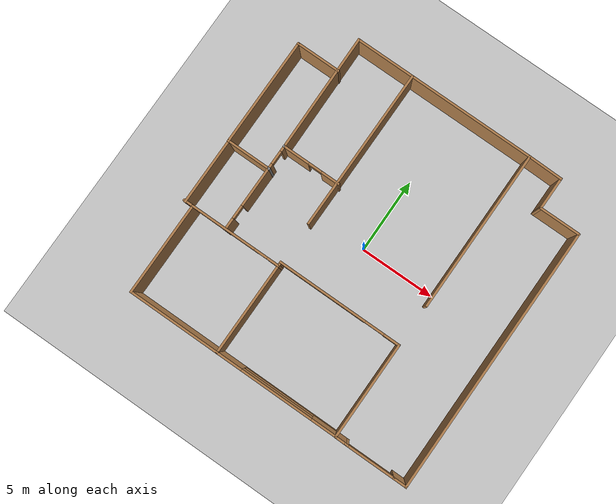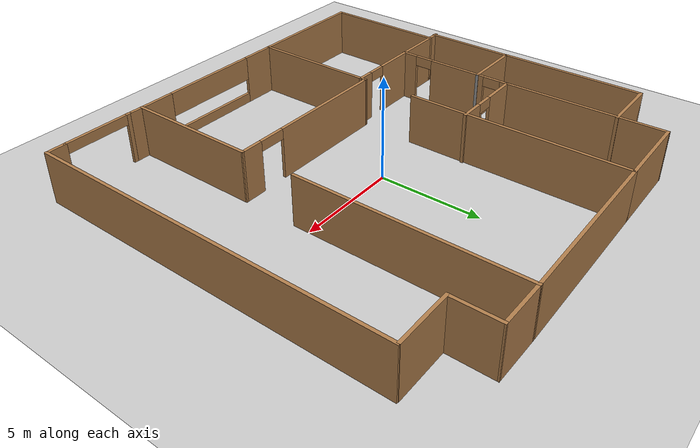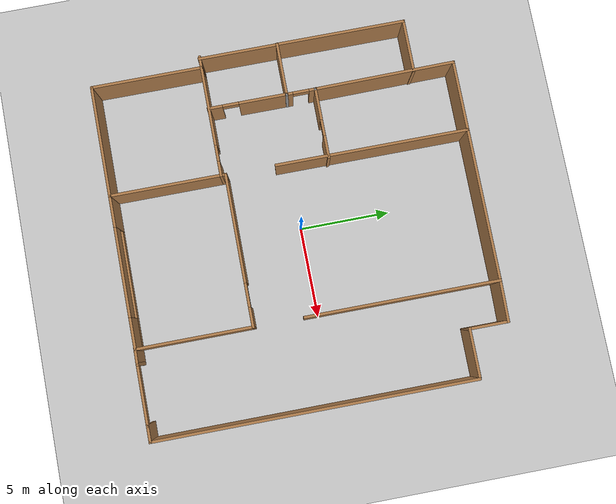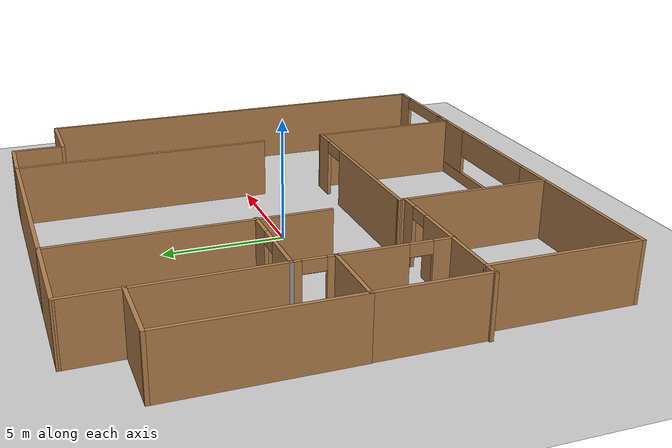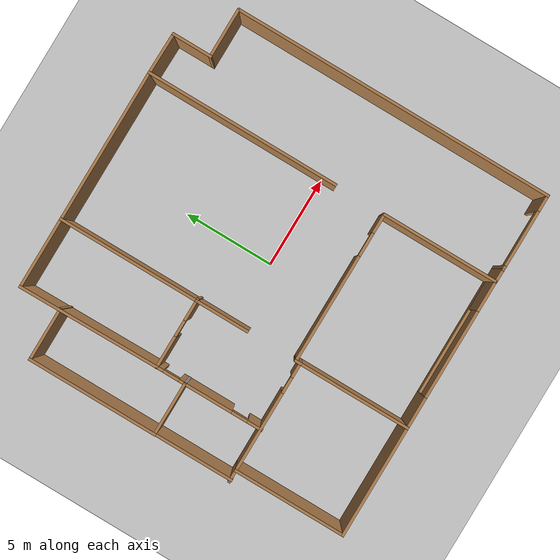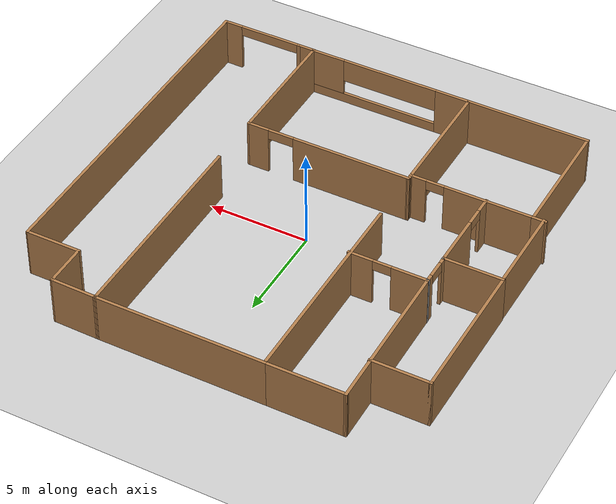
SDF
<sdf version="1.7">
 <world name="default">
  <light name="sun" type="directional">
   <pose>0 0 10 0 -0 0</pose>
   <diffuse>0.8 0.8 0.8 1</diffuse>
   <specular>0.2 0.2 0.2 1</specular>
   <attenuation>
    <range>1000</range>
    <constant>0.9</constant>
    <linear>0.01</linear>
    <quadratic>0.001</quadratic>
   </attenuation>
   <direction>-0.5 0.1 -0.9</direction>
   <spot><inner_angle>0</inner_angle><outer_angle>0</outer_angle><falloff>0</falloff></spot>
  </light>
  <model name="ground_plane">
   <static>1</static>
   <link name="link">
    <collision name="collision">
     <geometry><plane><normal>0 0 1</normal><size>100 100</size></plane></geometry>
     <surface><friction><ode><mu>100</mu><mu2>50</mu2></ode></friction></surface>
    </collision>
    <visual name="visual">
     <cast_shadows>0</cast_shadows>
     <geometry><plane><normal>0 0 1</normal><size>100 100</size></plane></geometry>
     <material>
      <script><uri>file://media/materials/scripts/gazebo.material</uri><name>Gazebo/Grey</name></script>
     </material>
    </visual>
   </link>
  </model>
  <gravity>0 0 -9.8</gravity>
  <magnetic_field>6e-06 2.3e-05 -4.2e-05</magnetic_field>
  <atmosphere type="adiabatic"/>
  <physics type="ode">
   <max_step_size>0.001</max_step_size>
   <real_time_factor>1</real_time_factor>
   <real_time_update_rate>1000</real_time_update_rate>
  </physics>
  <scene><ambient>0.4 0.4 0.4 1</ambient><background>0.7 0.7 0.7 1</background><shadows>1</shadows></scene>
  <audio><device>default</device></audio>
  <spherical_coordinates>
   <surface_model>EARTH_WGS84</surface_model>
   <latitude_deg>0</latitude_deg>
   <longitude_deg>0</longitude_deg>
   <elevation>0</elevation>
   <heading_deg>0</heading_deg>
  </spherical_coordinates>
  <model name="Silveroak-15">
   <link name="Wall_10">
    <pose>5.085 4.57986 0 0 -0 1.5708</pose>
    <inertial>
     <mass>1</mass>
     <inertia><ixx>1</ixx><ixy>0</ixy><ixz>0</ixz><iyy>1</iyy><iyz>0</iyz><izz>1</izz></inertia>
    </inertial>
    <visual name="Wall_10_Visual">
     <pose>0 0 1.25 0 -0 0</pose>
     <geometry><box><size>10.75 0.15 2.5</size></box></geometry>
     <material>
      <script><uri>file://media/materials/scripts/gazebo.material</uri><name>Gazebo/WoodFloor</name></script>
      <ambient>1 1 1 1</ambient>
      <shader type="pixel"><normal_map>__default__</normal_map></shader>
      <diffuse>0 0 0 1</diffuse>
      <specular>0 0 0 1</specular>
      <emissive>0 0 0 1</emissive>
     </material>
     <meta><layer>0</layer></meta>
    </visual>
    <collision name="Wall_10_Collision">
     <pose>0 0 1.25 0 -0 0</pose>
     <geometry><box><size>10.75 0.15 2.5</size></box></geometry>
     <surface>
      <friction>
       <ode><mu>1</mu><mu2>1</mu2><fdir1>0 0 0</fdir1><slip1>0</slip1><slip2>0</slip2></ode>
       <torsional>
        <coefficient>1</coefficient>
        <patch_radius>0</patch_radius>
        <surface_radius>0</surface_radius>
        <use_patch_radius>1</use_patch_radius>
        <ode><slip>0</slip></ode>
       </torsional>
      </friction>
      <bounce><restitution_coefficient>0</restitution_coefficient><threshold>1e+06</threshold></bounce>
      <contact>
       <collide_without_contact>0</collide_without_contact>
       <collide_without_contact_bitmask>1</collide_without_contact_bitmask>
       <collide_bitmask>1</collide_bitmask>
       <ode>
        <soft_cfm>0</soft_cfm>
        <soft_erp>0.2</soft_erp>
        <kp>1e+13</kp>
        <kd>1</kd>
        <max_vel>0.01</max_vel>
        <min_depth>0</min_depth>
       </ode>
       <bullet>
        <split_impulse>1</split_impulse>
        <split_impulse_penetration_threshold>-0.01</split_impulse_penetration_threshold>
        <soft_cfm>0</soft_cfm>
        <soft_erp>0.2</soft_erp>
        <kp>1e+13</kp>
        <kd>1</kd>
       </bullet>
      </contact>
     </surface>
    </collision>
   </link>
   <link name="Wall_16">
    <pose>-3.275 -6.68514 0 0 -0 1.5708</pose>
    <inertial>
     <mass>1</mass>
     <inertia><ixx>1</ixx><ixy>0</ixy><ixz>0</ixz><iyy>1</iyy><iyz>0</iyz><izz>1</izz></inertia>
    </inertial>
    <visual name="Wall_16_Visual">
     <pose>0 0 1.25 0 -0 0</pose>
     <geometry><box><size>6.5 0.15 2.5</size></box></geometry>
     <material>
      <script><uri>file://media/materials/scripts/gazebo.material</uri><name>Gazebo/WoodFloor</name></script>
      <ambient>1 1 1 1</ambient>
      <shader type="pixel"><normal_map>__default__</normal_map></shader>
      <diffuse>1 1 1 1</diffuse>
      <specular>0 0 0 1</specular>
      <emissive>0 0 0 1</emissive>
     </material>
     <meta><layer>0</layer></meta>
    </visual>
    <collision name="Wall_16_Collision">
     <pose>0 0 1.25 0 -0 0</pose>
     <geometry><box><size>6.5 0.15 2.5</size></box></geometry>
     <surface>
      <friction>
       <ode><mu>1</mu><mu2>1</mu2><fdir1>0 0 0</fdir1><slip1>0</slip1><slip2>0</slip2></ode>
       <torsional>
        <coefficient>1</coefficient>
        <patch_radius>0</patch_radius>
        <surface_radius>0</surface_radius>
        <use_patch_radius>1</use_patch_radius>
        <ode><slip>0</slip></ode>
       </torsional>
      </friction>
      <bounce><restitution_coefficient>0</restitution_coefficient><threshold>1e+06</threshold></bounce>
      <contact>
       <collide_without_contact>0</collide_without_contact>
       <collide_without_contact_bitmask>1</collide_without_contact_bitmask>
       <collide_bitmask>1</collide_bitmask>
       <ode>
        <soft_cfm>0</soft_cfm>
        <soft_erp>0.2</soft_erp>
        <kp>1e+13</kp>
        <kd>1</kd>
        <max_vel>0.01</max_vel>
        <min_depth>0</min_depth>
       </ode>
       <bullet>
        <split_impulse>1</split_impulse>
        <split_impulse_penetration_threshold>-0.01</split_impulse_penetration_threshold>
        <soft_cfm>0</soft_cfm>
        <soft_erp>0.2</soft_erp>
        <kp>1e+13</kp>
        <kd>1</kd>
       </bullet>
      </contact>
     </surface>
    </collision>
   </link>
   <link name="Wall_18">
    <pose>0.9 -9.86014 0 0 -0 0</pose>
    <inertial>
     <mass>1</mass>
     <inertia><ixx>1</ixx><ixy>0</ixy><ixz>0</ixz><iyy>1</iyy><iyz>0</iyz><izz>1</izz></inertia>
    </inertial>
    <visual name="Wall_18_Visual_3">
     <pose>0.010579 0 1.9 0 -0 0</pose>
     <geometry><box><size>4.91998 0.15 1.2</size></box></geometry>
     <material>
      <script><uri>file://media/materials/scripts/gazebo.material</uri><name>Gazebo/WoodFloor</name></script>
      <ambient>1 1 1 1</ambient>
      <shader type="pixel"><normal_map>__default__</normal_map></shader>
      <diffuse>0.7 0.7 0.7 1</diffuse>
      <specular>0.01 0.01 0.01 1</specular>
      <emissive>0 0 0 1</emissive>
     </material>
     <meta><layer>0</layer></meta>
    </visual>
    <visual name="Wall_18_Visual_2">
     <pose>3.36028 0 1.5 0 -0 0</pose>
     <geometry><box><size>1.77943 0.15 2</size></box></geometry>
     <material>
      <script><uri>file://media/materials/scripts/gazebo.material</uri><name>Gazebo/WoodFloor</name></script>
      <ambient>1 1 1 1</ambient>
      <shader type="pixel"><normal_map>__default__</normal_map></shader>
      <diffuse>0.7 0.7 0.7 1</diffuse>
      <specular>0.01 0.01 0.01 1</specular>
      <emissive>0 0 0 1</emissive>
     </material>
     <meta><layer>0</layer></meta>
    </visual>
    <visual name="Wall_18_Visual_0">
     <pose>-3.3497 0 1.25 0 -0 0</pose>
     <geometry><box><size>1.80059 0.15 2.5</size></box></geometry>
     <material>
      <script><uri>file://media/materials/scripts/gazebo.material</uri><name>Gazebo/WoodFloor</name></script>
      <ambient>1 1 1 1</ambient>
      <shader type="pixel"><normal_map>__default__</normal_map></shader>
      <diffuse>0.7 0.7 0.7 1</diffuse>
      <specular>0.01 0.01 0.01 1</specular>
      <emissive>0 0 0 1</emissive>
     </material>
     <meta><layer>0</layer></meta>
    </visual>
    <visual name="Wall_18_Visual_1">
     <pose>0.900296 0 0.25 0 -0 0</pose>
     <geometry><box><size>6.69941 0.15 0.5</size></box></geometry>
     <material>
      <script><uri>file://media/materials/scripts/gazebo.material</uri><name>Gazebo/WoodFloor</name></script>
      <ambient>1 1 1 1</ambient>
      <shader type="pixel"><normal_map>__default__</normal_map></shader>
      <diffuse>1 1 1 1</diffuse>
      <specular>0 0 0 1</specular>
      <emissive>0 0 0 1</emissive>
     </material>
     <meta><layer>0</layer></meta>
    </visual>
    <collision name="Wall_18_Collision_2">
     <pose>3.36028 0 1.5 0 -0 0</pose>
     <geometry><box><size>1.77943 0.15 2</size></box></geometry>
     <surface>
      <friction>
       <ode><mu>1</mu><mu2>1</mu2><fdir1>0 0 0</fdir1><slip1>0</slip1><slip2>0</slip2></ode>
       <torsional>
        <coefficient>1</coefficient>
        <patch_radius>0</patch_radius>
        <surface_radius>0</surface_radius>
        <use_patch_radius>1</use_patch_radius>
        <ode><slip>0</slip></ode>
       </torsional>
      </friction>
      <bounce><restitution_coefficient>0</restitution_coefficient><threshold>1e+06</threshold></bounce>
      <contact>
       <collide_without_contact>0</collide_without_contact>
       <collide_without_contact_bitmask>1</collide_without_contact_bitmask>
       <collide_bitmask>1</collide_bitmask>
       <ode>
        <soft_cfm>0</soft_cfm>
        <soft_erp>0.2</soft_erp>
        <kp>1e+13</kp>
        <kd>1</kd>
        <max_vel>0.01</max_vel>
        <min_depth>0</min_depth>
       </ode>
       <bullet>
        <split_impulse>1</split_impulse>
        <split_impulse_penetration_threshold>-0.01</split_impulse_penetration_threshold>
        <soft_cfm>0</soft_cfm>
        <soft_erp>0.2</soft_erp>
        <kp>1e+13</kp>
        <kd>1</kd>
       </bullet>
      </contact>
     </surface>
    </collision>
    <collision name="Wall_18_Collision_1">
     <pose>0.900296 0 0.25 0 -0 0</pose>
     <geometry><box><size>6.69941 0.15 0.5</size></box></geometry>
     <surface>
      <friction>
       <ode><mu>1</mu><mu2>1</mu2><fdir1>0 0 0</fdir1><slip1>0</slip1><slip2>0</slip2></ode>
       <torsional>
        <coefficient>1</coefficient>
        <patch_radius>0</patch_radius>
        <surface_radius>0</surface_radius>
        <use_patch_radius>1</use_patch_radius>
        <ode><slip>0</slip></ode>
       </torsional>
      </friction>
      <bounce><restitution_coefficient>0</restitution_coefficient><threshold>1e+06</threshold></bounce>
      <contact>
       <collide_without_contact>0</collide_without_contact>
       <collide_without_contact_bitmask>1</collide_without_contact_bitmask>
       <collide_bitmask>1</collide_bitmask>
       <ode>
        <soft_cfm>0</soft_cfm>
        <soft_erp>0.2</soft_erp>
        <kp>1e+13</kp>
        <kd>1</kd>
        <max_vel>0.01</max_vel>
        <min_depth>0</min_depth>
       </ode>
       <bullet>
        <split_impulse>1</split_impulse>
        <split_impulse_penetration_threshold>-0.01</split_impulse_penetration_threshold>
        <soft_cfm>0</soft_cfm>
        <soft_erp>0.2</soft_erp>
        <kp>1e+13</kp>
        <kd>1</kd>
       </bullet>
      </contact>
     </surface>
    </collision>
    <collision name="Wall_18_Collision_0">
     <pose>-3.3497 0 1.25 0 -0 0</pose>
     <geometry><box><size>1.80059 0.15 2.5</size></box></geometry>
     <surface>
      <friction>
       <ode><mu>1</mu><mu2>1</mu2><fdir1>0 0 0</fdir1><slip1>0</slip1><slip2>0</slip2></ode>
       <torsional>
        <coefficient>1</coefficient>
        <patch_radius>0</patch_radius>
        <surface_radius>0</surface_radius>
        <use_patch_radius>1</use_patch_radius>
        <ode><slip>0</slip></ode>
       </torsional>
      </friction>
      <bounce><restitution_coefficient>0</restitution_coefficient><threshold>1e+06</threshold></bounce>
      <contact>
       <collide_without_contact>0</collide_without_contact>
       <collide_without_contact_bitmask>1</collide_without_contact_bitmask>
       <collide_bitmask>1</collide_bitmask>
       <ode>
        <soft_cfm>0</soft_cfm>
        <soft_erp>0.2</soft_erp>
        <kp>1e+13</kp>
        <kd>1</kd>
        <max_vel>0.01</max_vel>
        <min_depth>0</min_depth>
       </ode>
       <bullet>
        <split_impulse>1</split_impulse>
        <split_impulse_penetration_threshold>-0.01</split_impulse_penetration_threshold>
        <soft_cfm>0</soft_cfm>
        <soft_erp>0.2</soft_erp>
        <kp>1e+13</kp>
        <kd>1</kd>
       </bullet>
      </contact>
     </surface>
    </collision>
    <collision name="Wall_18_Collision_3">
     <pose>0.010579 0 1.9 0 -0 0</pose>
     <geometry><box><size>4.91998 0.15 1.2</size></box></geometry>
     <surface>
      <friction>
       <ode><mu>1</mu><mu2>1</mu2><fdir1>0 0 0</fdir1><slip1>0</slip1><slip2>0</slip2></ode>
       <torsional>
        <coefficient>1</coefficient>
        <patch_radius>0</patch_radius>
        <surface_radius>0</surface_radius>
        <use_patch_radius>1</use_patch_radius>
        <ode><slip>0</slip></ode>
       </torsional>
      </friction>
      <bounce><restitution_coefficient>0</restitution_coefficient><threshold>1e+06</threshold></bounce>
      <contact>
       <collide_without_contact>0</collide_without_contact>
       <collide_without_contact_bitmask>1</collide_without_contact_bitmask>
       <collide_bitmask>1</collide_bitmask>
       <ode>
        <soft_cfm>0</soft_cfm>
        <soft_erp>0.2</soft_erp>
        <kp>1e+13</kp>
        <kd>1</kd>
        <max_vel>0.01</max_vel>
        <min_depth>0</min_depth>
       </ode>
       <bullet>
        <split_impulse>1</split_impulse>
        <split_impulse_penetration_threshold>-0.01</split_impulse_penetration_threshold>
        <soft_cfm>0</soft_cfm>
        <soft_erp>0.2</soft_erp>
        <kp>1e+13</kp>
        <kd>1</kd>
       </bullet>
      </contact>
     </surface>
    </collision>
   </link>
   <link name="Wall_20">
    <pose>0.9 -3.51514 0 0 -0 3.14039</pose>
    <inertial>
     <mass>1</mass>
     <inertia><ixx>1</ixx><ixy>0</ixy><ixz>0</ixz><iyy>1</iyy><iyz>0</iyz><izz>1</izz></inertia>
    </inertial>
    <visual name="Wall_20_Visual_1">
     <pose>1.22365 0 1.25 0 -0 0</pose>
     <geometry><box><size>6.05271 0.15 2.5</size></box></geometry>
     <material>
      <script><uri>file://media/materials/scripts/gazebo.material</uri><name>Gazebo/WoodFloor</name></script>
      <ambient>1 1 1 1</ambient>
      <shader type="pixel"><normal_map>__default__</normal_map></shader>
      <diffuse>1 1 1 1</diffuse>
      <specular>0 0 0 1</specular>
      <emissive>0 0 0 1</emissive>
     </material>
     <meta><layer>0</layer></meta>
    </visual>
    <visual name="Wall_20_Visual_2">
     <pose>-2.45777 0 2.25 0 -0 0</pose>
     <geometry><box><size>1.31012 0.15 0.5</size></box></geometry>
     <material>
      <script><uri>file://media/materials/scripts/gazebo.material</uri><name>Gazebo/WoodFloor</name></script>
      <ambient>1 1 1 1</ambient>
      <shader type="pixel"><normal_map>__default__</normal_map></shader>
      <diffuse>0.7 0.7 0.7 1</diffuse>
      <specular>0.01 0.01 0.01 1</specular>
      <emissive>0 0 0 1</emissive>
     </material>
     <meta><layer>0</layer></meta>
    </visual>
    <visual name="Wall_20_Visual_0">
     <pose>-3.68142 0 1.25 0 -0 0</pose>
     <geometry><box><size>1.13717 0.15 2.5</size></box></geometry>
     <material>
      <script><uri>file://media/materials/scripts/gazebo.material</uri><name>Gazebo/WoodFloor</name></script>
      <ambient>1 1 1 1</ambient>
      <shader type="pixel"><normal_map>__default__</normal_map></shader>
      <diffuse>0.7 0.7 0.7 1</diffuse>
      <specular>0.01 0.01 0.01 1</specular>
      <emissive>0 0 0 1</emissive>
     </material>
     <meta><layer>0</layer></meta>
    </visual>
    <collision name="Wall_20_Collision_2">
     <pose>-2.45777 0 2.25 0 -0 0</pose>
     <geometry><box><size>1.31012 0.15 0.5</size></box></geometry>
     <surface>
      <friction>
       <ode><mu>1</mu><mu2>1</mu2><fdir1>0 0 0</fdir1><slip1>0</slip1><slip2>0</slip2></ode>
       <torsional>
        <coefficient>1</coefficient>
        <patch_radius>0</patch_radius>
        <surface_radius>0</surface_radius>
        <use_patch_radius>1</use_patch_radius>
        <ode><slip>0</slip></ode>
       </torsional>
      </friction>
      <bounce><restitution_coefficient>0</restitution_coefficient><threshold>1e+06</threshold></bounce>
      <contact>
       <collide_without_contact>0</collide_without_contact>
       <collide_without_contact_bitmask>1</collide_without_contact_bitmask>
       <collide_bitmask>1</collide_bitmask>
       <ode>
        <soft_cfm>0</soft_cfm>
        <soft_erp>0.2</soft_erp>
        <kp>1e+13</kp>
        <kd>1</kd>
        <max_vel>0.01</max_vel>
        <min_depth>0</min_depth>
       </ode>
       <bullet>
        <split_impulse>1</split_impulse>
        <split_impulse_penetration_threshold>-0.01</split_impulse_penetration_threshold>
        <soft_cfm>0</soft_cfm>
        <soft_erp>0.2</soft_erp>
        <kp>1e+13</kp>
        <kd>1</kd>
       </bullet>
      </contact>
     </surface>
    </collision>
    <collision name="Wall_20_Collision_1">
     <pose>1.22365 0 1.25 0 -0 0</pose>
     <geometry><box><size>6.05271 0.15 2.5</size></box></geometry>
     <surface>
      <friction>
       <ode><mu>1</mu><mu2>1</mu2><fdir1>0 0 0</fdir1><slip1>0</slip1><slip2>0</slip2></ode>
       <torsional>
        <coefficient>1</coefficient>
        <patch_radius>0</patch_radius>
        <surface_radius>0</surface_radius>
        <use_patch_radius>1</use_patch_radius>
        <ode><slip>0</slip></ode>
       </torsional>
      </friction>
      <bounce><restitution_coefficient>0</restitution_coefficient><threshold>1e+06</threshold></bounce>
      <contact>
       <collide_without_contact>0</collide_without_contact>
       <collide_without_contact_bitmask>1</collide_without_contact_bitmask>
       <collide_bitmask>1</collide_bitmask>
       <ode>
        <soft_cfm>0</soft_cfm>
        <soft_erp>0.2</soft_erp>
        <kp>1e+13</kp>
        <kd>1</kd>
        <max_vel>0.01</max_vel>
        <min_depth>0</min_depth>
       </ode>
       <bullet>
        <split_impulse>1</split_impulse>
        <split_impulse_penetration_threshold>-0.01</split_impulse_penetration_threshold>
        <soft_cfm>0</soft_cfm>
        <soft_erp>0.2</soft_erp>
        <kp>1e+13</kp>
        <kd>1</kd>
       </bullet>
      </contact>
     </surface>
    </collision>
    <collision name="Wall_20_Collision_0">
     <pose>-3.68142 0 1.25 0 -0 0</pose>
     <geometry><box><size>1.13717 0.15 2.5</size></box></geometry>
     <surface>
      <friction>
       <ode><mu>1</mu><mu2>1</mu2><fdir1>0 0 0</fdir1><slip1>0</slip1><slip2>0</slip2></ode>
       <torsional>
        <coefficient>1</coefficient>
        <patch_radius>0</patch_radius>
        <surface_radius>0</surface_radius>
        <use_patch_radius>1</use_patch_radius>
        <ode><slip>0</slip></ode>
       </torsional>
      </friction>
      <bounce><restitution_coefficient>0</restitution_coefficient><threshold>1e+06</threshold></bounce>
      <contact>
       <collide_without_contact>0</collide_without_contact>
       <collide_without_contact_bitmask>1</collide_without_contact_bitmask>
       <collide_bitmask>1</collide_bitmask>
       <ode>
        <soft_cfm>0</soft_cfm>
        <soft_erp>0.2</soft_erp>
        <kp>1e+13</kp>
        <kd>1</kd>
        <max_vel>0.01</max_vel>
        <min_depth>0</min_depth>
       </ode>
       <bullet>
        <split_impulse>1</split_impulse>
        <split_impulse_penetration_threshold>-0.01</split_impulse_penetration_threshold>
        <soft_cfm>0</soft_cfm>
        <soft_erp>0.2</soft_erp>
        <kp>1e+13</kp>
        <kd>1</kd>
       </bullet>
      </contact>
     </surface>
    </collision>
   </link>
   <link name="Wall_23">
    <pose>-6.325 -9.86014 0 0 -0 3.14159</pose>
    <inertial>
     <mass>1</mass>
     <inertia><ixx>1</ixx><ixy>0</ixy><ixz>0</ixz><iyy>1</iyy><iyz>0</iyz><izz>1</izz></inertia>
    </inertial>
    <visual name="Wall_23_Visual">
     <pose>0 0 1.25 0 -0 0</pose>
     <geometry><box><size>6.25 0.15 2.5</size></box></geometry>
     <material>
      <script><uri>file://media/materials/scripts/gazebo.material</uri><name>Gazebo/WoodFloor</name></script>
      <ambient>1 1 1 1</ambient>
      <shader type="pixel"><normal_map>__default__</normal_map></shader>
      <diffuse>1 1 1 1</diffuse>
      <specular>0 0 0 1</specular>
      <emissive>0 0 0 1</emissive>
     </material>
     <meta><layer>0</layer></meta>
    </visual>
    <collision name="Wall_23_Collision">
     <pose>0 0 1.25 0 -0 0</pose>
     <geometry><box><size>6.25 0.15 2.5</size></box></geometry>
     <surface>
      <friction>
       <ode><mu>1</mu><mu2>1</mu2><fdir1>0 0 0</fdir1><slip1>0</slip1><slip2>0</slip2></ode>
       <torsional>
        <coefficient>1</coefficient>
        <patch_radius>0</patch_radius>
        <surface_radius>0</surface_radius>
        <use_patch_radius>1</use_patch_radius>
        <ode><slip>0</slip></ode>
       </torsional>
      </friction>
      <bounce><restitution_coefficient>0</restitution_coefficient><threshold>1e+06</threshold></bounce>
      <contact>
       <collide_without_contact>0</collide_without_contact>
       <collide_without_contact_bitmask>1</collide_without_contact_bitmask>
       <collide_bitmask>1</collide_bitmask>
       <ode>
        <soft_cfm>0</soft_cfm>
        <soft_erp>0.2</soft_erp>
        <kp>1e+13</kp>
        <kd>1</kd>
        <max_vel>0.01</max_vel>
        <min_depth>0</min_depth>
       </ode>
       <bullet>
        <split_impulse>1</split_impulse>
        <split_impulse_penetration_threshold>-0.01</split_impulse_penetration_threshold>
        <soft_cfm>0</soft_cfm>
        <soft_erp>0.2</soft_erp>
        <kp>1e+13</kp>
        <kd>1</kd>
       </bullet>
      </contact>
     </surface>
    </collision>
   </link>
   <link name="Wall_26">
    <pose>-9.375 -6.81014 0 0 -0 1.5708</pose>
    <inertial>
     <mass>1</mass>
     <inertia><ixx>1</ixx><ixy>0</ixy><ixz>0</ixz><iyy>1</iyy><iyz>0</iyz><izz>1</izz></inertia>
    </inertial>
    <visual name="Wall_26_Visual">
     <pose>0 0 1.25 0 -0 0</pose>
     <geometry><box><size>6.25 0.15 2.5</size></box></geometry>
     <material>
      <script><uri>file://media/materials/scripts/gazebo.material</uri><name>Gazebo/WoodFloor</name></script>
      <ambient>1 1 1 1</ambient>
      <shader type="pixel"><normal_map>__default__</normal_map></shader>
      <diffuse>1 1 1 1</diffuse>
      <specular>0 0 0 1</specular>
      <emissive>0 0 0 1</emissive>
     </material>
     <meta><layer>0</layer></meta>
    </visual>
    <collision name="Wall_26_Collision">
     <pose>0 0 1.25 0 -0 0</pose>
     <geometry><box><size>6.25 0.15 2.5</size></box></geometry>
     <surface>
      <friction>
       <ode><mu>1</mu><mu2>1</mu2><fdir1>0 0 0</fdir1><slip1>0</slip1><slip2>0</slip2></ode>
       <torsional>
        <coefficient>1</coefficient>
        <patch_radius>0</patch_radius>
        <surface_radius>0</surface_radius>
        <use_patch_radius>1</use_patch_radius>
        <ode><slip>0</slip></ode>
       </torsional>
      </friction>
      <bounce><restitution_coefficient>0</restitution_coefficient><threshold>1e+06</threshold></bounce>
      <contact>
       <collide_without_contact>0</collide_without_contact>
       <collide_without_contact_bitmask>1</collide_without_contact_bitmask>
       <collide_bitmask>1</collide_bitmask>
       <ode>
        <soft_cfm>0</soft_cfm>
        <soft_erp>0.2</soft_erp>
        <kp>1e+13</kp>
        <kd>1</kd>
        <max_vel>0.01</max_vel>
        <min_depth>0</min_depth>
       </ode>
       <bullet>
        <split_impulse>1</split_impulse>
        <split_impulse_penetration_threshold>-0.01</split_impulse_penetration_threshold>
        <soft_cfm>0</soft_cfm>
        <soft_erp>0.2</soft_erp>
        <kp>1e+13</kp>
        <kd>1</kd>
       </bullet>
      </contact>
     </surface>
    </collision>
   </link>
   <link name="Wall_28">
    <pose>-6.325 -3.76014 0 0 -0 0</pose>
    <inertial>
     <mass>1</mass>
     <inertia><ixx>1</ixx><ixy>0</ixy><ixz>0</ixz><iyy>1</iyy><iyz>0</iyz><izz>1</izz></inertia>
    </inertial>
    <visual name="Wall_28_Visual_1">
     <pose>2.6925 0 1.25 0 -0 0</pose>
     <geometry><box><size>0.865 0.15 2.5</size></box></geometry>
     <material>
      <script><uri>file://media/materials/scripts/gazebo.material</uri><name>Gazebo/WoodFloor</name></script>
      <ambient>1 1 1 1</ambient>
      <shader type="pixel"><normal_map>__default__</normal_map></shader>
      <diffuse>0.7 0.7 0.7 1</diffuse>
      <specular>0.01 0.01 0.01 1</specular>
      <emissive>0 0 0 1</emissive>
     </material>
     <meta><layer>0</layer></meta>
    </visual>
    <visual name="Wall_28_Visual_2">
     <pose>1.81 0 2.25 0 -0 0</pose>
     <geometry><box><size>0.9 0.15 0.5</size></box></geometry>
     <material>
      <script><uri>file://media/materials/scripts/gazebo.material</uri><name>Gazebo/WoodFloor</name></script>
      <ambient>1 1 1 1</ambient>
      <shader type="pixel"><normal_map>__default__</normal_map></shader>
      <diffuse>0.7 0.7 0.7 1</diffuse>
      <specular>0.01 0.01 0.01 1</specular>
      <emissive>0 0 0 1</emissive>
     </material>
     <meta><layer>0</layer></meta>
    </visual>
    <visual name="Wall_28_Visual_0">
     <pose>-0.8825 0 1.25 0 -0 0</pose>
     <geometry><box><size>4.485 0.15 2.5</size></box></geometry>
     <material>
      <script><uri>file://media/materials/scripts/gazebo.material</uri><name>Gazebo/WoodFloor</name></script>
      <ambient>1 1 1 1</ambient>
      <shader type="pixel"><normal_map>__default__</normal_map></shader>
      <diffuse>1 1 1 1</diffuse>
      <specular>0 0 0 1</specular>
      <emissive>0 0 0 1</emissive>
     </material>
     <meta><layer>0</layer></meta>
    </visual>
    <collision name="Wall_28_Collision_1">
     <pose>2.6925 0 1.25 0 -0 0</pose>
     <geometry><box><size>0.865 0.15 2.5</size></box></geometry>
     <surface>
      <friction>
       <ode><mu>1</mu><mu2>1</mu2><fdir1>0 0 0</fdir1><slip1>0</slip1><slip2>0</slip2></ode>
       <torsional>
        <coefficient>1</coefficient>
        <patch_radius>0</patch_radius>
        <surface_radius>0</surface_radius>
        <use_patch_radius>1</use_patch_radius>
        <ode><slip>0</slip></ode>
       </torsional>
      </friction>
      <bounce><restitution_coefficient>0</restitution_coefficient><threshold>1e+06</threshold></bounce>
      <contact>
       <collide_without_contact>0</collide_without_contact>
       <collide_without_contact_bitmask>1</collide_without_contact_bitmask>
       <collide_bitmask>1</collide_bitmask>
       <ode>
        <soft_cfm>0</soft_cfm>
        <soft_erp>0.2</soft_erp>
        <kp>1e+13</kp>
        <kd>1</kd>
        <max_vel>0.01</max_vel>
        <min_depth>0</min_depth>
       </ode>
       <bullet>
        <split_impulse>1</split_impulse>
        <split_impulse_penetration_threshold>-0.01</split_impulse_penetration_threshold>
        <soft_cfm>0</soft_cfm>
        <soft_erp>0.2</soft_erp>
        <kp>1e+13</kp>
        <kd>1</kd>
       </bullet>
      </contact>
     </surface>
    </collision>
    <collision name="Wall_28_Collision_2">
     <pose>1.81 0 2.25 0 -0 0</pose>
     <geometry><box><size>0.9 0.15 0.5</size></box></geometry>
     <surface>
      <friction>
       <ode><mu>1</mu><mu2>1</mu2><fdir1>0 0 0</fdir1><slip1>0</slip1><slip2>0</slip2></ode>
       <torsional>
        <coefficient>1</coefficient>
        <patch_radius>0</patch_radius>
        <surface_radius>0</surface_radius>
        <use_patch_radius>1</use_patch_radius>
        <ode><slip>0</slip></ode>
       </torsional>
      </friction>
      <bounce><restitution_coefficient>0</restitution_coefficient><threshold>1e+06</threshold></bounce>
      <contact>
       <collide_without_contact>0</collide_without_contact>
       <collide_without_contact_bitmask>1</collide_without_contact_bitmask>
       <collide_bitmask>1</collide_bitmask>
       <ode>
        <soft_cfm>0</soft_cfm>
        <soft_erp>0.2</soft_erp>
        <kp>1e+13</kp>
        <kd>1</kd>
        <max_vel>0.01</max_vel>
        <min_depth>0</min_depth>
       </ode>
       <bullet>
        <split_impulse>1</split_impulse>
        <split_impulse_penetration_threshold>-0.01</split_impulse_penetration_threshold>
        <soft_cfm>0</soft_cfm>
        <soft_erp>0.2</soft_erp>
        <kp>1e+13</kp>
        <kd>1</kd>
       </bullet>
      </contact>
     </surface>
    </collision>
    <collision name="Wall_28_Collision_0">
     <pose>-0.8825 0 1.25 0 -0 0</pose>
     <geometry><box><size>4.485 0.15 2.5</size></box></geometry>
     <surface>
      <friction>
       <ode><mu>1</mu><mu2>1</mu2><fdir1>0 0 0</fdir1><slip1>0</slip1><slip2>0</slip2></ode>
       <torsional>
        <coefficient>1</coefficient>
        <patch_radius>0</patch_radius>
        <surface_radius>0</surface_radius>
        <use_patch_radius>1</use_patch_radius>
        <ode><slip>0</slip></ode>
       </torsional>
      </friction>
      <bounce><restitution_coefficient>0</restitution_coefficient><threshold>1e+06</threshold></bounce>
      <contact>
       <collide_without_contact>0</collide_without_contact>
       <collide_without_contact_bitmask>1</collide_without_contact_bitmask>
       <collide_bitmask>1</collide_bitmask>
       <ode>
        <soft_cfm>0</soft_cfm>
        <soft_erp>0.2</soft_erp>
        <kp>1e+13</kp>
        <kd>1</kd>
        <max_vel>0.01</max_vel>
        <min_depth>0</min_depth>
       </ode>
       <bullet>
        <split_impulse>1</split_impulse>
        <split_impulse_penetration_threshold>-0.01</split_impulse_penetration_threshold>
        <soft_cfm>0</soft_cfm>
        <soft_erp>0.2</soft_erp>
        <kp>1e+13</kp>
        <kd>1</kd>
       </bullet>
      </contact>
     </surface>
    </collision>
   </link>
   <link name="Wall_31">
    <pose>-3.265 4.57986 0 0 -0 1.5708</pose>
    <inertial>
     <mass>1</mass>
     <inertia><ixx>1</ixx><ixy>0</ixy><ixz>0</ixz><iyy>1</iyy><iyz>0</iyz><izz>1</izz></inertia>
    </inertial>
    <visual name="Wall_31_Visual">
     <pose>0 0 1.25 0 -0 0</pose>
     <geometry><box><size>10.75 0.15 2.5</size></box></geometry>
     <material>
      <script><uri>file://media/materials/scripts/gazebo.material</uri><name>Gazebo/WoodFloor</name></script>
      <ambient>1 1 1 1</ambient>
      <shader type="pixel"><normal_map>__default__</normal_map></shader>
      <diffuse>1 1 1 1</diffuse>
      <specular>0 0 0 1</specular>
      <emissive>0 0 0 1</emissive>
     </material>
     <meta><layer>0</layer></meta>
    </visual>
    <collision name="Wall_31_Collision">
     <pose>0 0 1.25 0 -0 0</pose>
     <geometry><box><size>10.75 0.15 2.5</size></box></geometry>
     <surface>
      <friction>
       <ode><mu>1</mu><mu2>1</mu2><fdir1>0 0 0</fdir1><slip1>0</slip1><slip2>0</slip2></ode>
       <torsional>
        <coefficient>1</coefficient>
        <patch_radius>0</patch_radius>
        <surface_radius>0</surface_radius>
        <use_patch_radius>1</use_patch_radius>
        <ode><slip>0</slip></ode>
       </torsional>
      </friction>
      <bounce><restitution_coefficient>0</restitution_coefficient><threshold>1e+06</threshold></bounce>
      <contact>
       <collide_without_contact>0</collide_without_contact>
       <collide_without_contact_bitmask>1</collide_without_contact_bitmask>
       <collide_bitmask>1</collide_bitmask>
       <ode>
        <soft_cfm>0</soft_cfm>
        <soft_erp>0.2</soft_erp>
        <kp>1e+13</kp>
        <kd>1</kd>
        <max_vel>0.01</max_vel>
        <min_depth>0</min_depth>
       </ode>
       <bullet>
        <split_impulse>1</split_impulse>
        <split_impulse_penetration_threshold>-0.01</split_impulse_penetration_threshold>
        <soft_cfm>0</soft_cfm>
        <soft_erp>0.2</soft_erp>
        <kp>1e+13</kp>
        <kd>1</kd>
       </bullet>
      </contact>
     </surface>
    </collision>
   </link>
   <link name="Wall_33">
    <pose>0.91 9.87986 0 0 -0 0</pose>
    <inertial>
     <mass>1</mass>
     <inertia><ixx>1</ixx><ixy>0</ixy><ixz>0</ixz><iyy>1</iyy><iyz>0</iyz><izz>1</izz></inertia>
    </inertial>
    <visual name="Wall_33_Visual">
     <pose>0 0 1.25 0 -0 0</pose>
     <geometry><box><size>8.5 0.15 2.5</size></box></geometry>
     <material>
      <script><uri>file://media/materials/scripts/gazebo.material</uri><name>Gazebo/WoodFloor</name></script>
      <ambient>1 1 1 1</ambient>
      <shader type="pixel"><normal_map>__default__</normal_map></shader>
      <diffuse>1 1 1 1</diffuse>
      <specular>0 0 0 1</specular>
      <emissive>0 0 0 1</emissive>
     </material>
     <meta><layer>0</layer></meta>
    </visual>
    <collision name="Wall_33_Collision">
     <pose>0 0 1.25 0 -0 0</pose>
     <geometry><box><size>8.5 0.15 2.5</size></box></geometry>
     <surface>
      <friction>
       <ode><mu>1</mu><mu2>1</mu2><fdir1>0 0 0</fdir1><slip1>0</slip1><slip2>0</slip2></ode>
       <torsional>
        <coefficient>1</coefficient>
        <patch_radius>0</patch_radius>
        <surface_radius>0</surface_radius>
        <use_patch_radius>1</use_patch_radius>
        <ode><slip>0</slip></ode>
       </torsional>
      </friction>
      <bounce><restitution_coefficient>0</restitution_coefficient><threshold>1e+06</threshold></bounce>
      <contact>
       <collide_without_contact>0</collide_without_contact>
       <collide_without_contact_bitmask>1</collide_without_contact_bitmask>
       <collide_bitmask>1</collide_bitmask>
       <ode>
        <soft_cfm>0</soft_cfm>
        <soft_erp>0.2</soft_erp>
        <kp>1e+13</kp>
        <kd>1</kd>
        <max_vel>0.01</max_vel>
        <min_depth>0</min_depth>
       </ode>
       <bullet>
        <split_impulse>1</split_impulse>
        <split_impulse_penetration_threshold>-0.01</split_impulse_penetration_threshold>
        <soft_cfm>0</soft_cfm>
        <soft_erp>0.2</soft_erp>
        <kp>1e+13</kp>
        <kd>1</kd>
       </bullet>
      </contact>
     </surface>
    </collision>
   </link>
   <link name="Wall_36">
    <pose>-9.905 4.09986 0 0 0 -1.5708</pose>
    <inertial>
     <mass>1</mass>
     <inertia><ixx>1</ixx><ixy>0</ixy><ixz>0</ixz><iyy>1</iyy><iyz>0</iyz><izz>1</izz></inertia>
    </inertial>
    <visual name="Wall_36_Visual">
     <pose>0 0 1.25 0 -0 0</pose>
     <geometry><box><size>7.25 0.15 2.5</size></box></geometry>
     <material>
      <script><uri>file://media/materials/scripts/gazebo.material</uri><name>Gazebo/WoodFloor</name></script>
      <ambient>1 1 1 1</ambient>
      <shader type="pixel"><normal_map>__default__</normal_map></shader>
      <diffuse>1 1 1 1</diffuse>
      <specular>0 0 0 1</specular>
      <emissive>0 0 0 1</emissive>
     </material>
     <meta><layer>0</layer></meta>
    </visual>
    <collision name="Wall_36_Collision">
     <pose>0 0 1.25 0 -0 0</pose>
     <geometry><box><size>7.25 0.15 2.5</size></box></geometry>
     <surface>
      <friction>
       <ode><mu>1</mu><mu2>1</mu2><fdir1>0 0 0</fdir1><slip1>0</slip1><slip2>0</slip2></ode>
       <torsional>
        <coefficient>1</coefficient>
        <patch_radius>0</patch_radius>
        <surface_radius>0</surface_radius>
        <use_patch_radius>1</use_patch_radius>
        <ode><slip>0</slip></ode>
       </torsional>
      </friction>
      <bounce><restitution_coefficient>0</restitution_coefficient><threshold>1e+06</threshold></bounce>
      <contact>
       <collide_without_contact>0</collide_without_contact>
       <collide_without_contact_bitmask>1</collide_without_contact_bitmask>
       <collide_bitmask>1</collide_bitmask>
       <ode>
        <soft_cfm>0</soft_cfm>
        <soft_erp>0.2</soft_erp>
        <kp>1e+13</kp>
        <kd>1</kd>
        <max_vel>0.01</max_vel>
        <min_depth>0</min_depth>
       </ode>
       <bullet>
        <split_impulse>1</split_impulse>
        <split_impulse_penetration_threshold>-0.01</split_impulse_penetration_threshold>
        <soft_cfm>0</soft_cfm>
        <soft_erp>0.2</soft_erp>
        <kp>1e+13</kp>
        <kd>1</kd>
       </bullet>
      </contact>
     </surface>
    </collision>
   </link>
   <link name="Wall_39">
    <pose>-7.04 2.15986 0 0 -0 0</pose>
    <visual name="Wall_39_Visual">
     <pose>0 0 1.25 0 -0 0</pose>
     <geometry><box><size>0.16 0.15 2.5</size></box></geometry>
     <material>
      <script><uri>file://media/materials/scripts/gazebo.material</uri><name>Gazebo/Grey</name></script>
      <ambient>1 1 1 1</ambient>
      <shader type="pixel"/>
     </material>
     <meta><layer>0</layer></meta>
    </visual>
    <collision name="Wall_39_Collision">
     <pose>0 0 1.25 0 -0 0</pose>
     <geometry><box><size>0.16 0.15 2.5</size></box></geometry>
     <surface>
      <friction>
       <ode><mu>1</mu><mu2>1</mu2><fdir1>0 0 0</fdir1><slip1>0</slip1><slip2>0</slip2></ode>
       <torsional>
        <coefficient>1</coefficient>
        <patch_radius>0</patch_radius>
        <surface_radius>0</surface_radius>
        <use_patch_radius>1</use_patch_radius>
        <ode><slip>0</slip></ode>
       </torsional>
      </friction>
      <bounce><restitution_coefficient>0</restitution_coefficient><threshold>1e+06</threshold></bounce>
      <contact>
       <collide_without_contact>0</collide_without_contact>
       <collide_without_contact_bitmask>1</collide_without_contact_bitmask>
       <collide_bitmask>1</collide_bitmask>
       <ode>
        <soft_cfm>0</soft_cfm>
        <soft_erp>0.2</soft_erp>
        <kp>1e+13</kp>
        <kd>1</kd>
        <max_vel>0.01</max_vel>
        <min_depth>0</min_depth>
       </ode>
       <bullet>
        <split_impulse>1</split_impulse>
        <split_impulse_penetration_threshold>-0.01</split_impulse_penetration_threshold>
        <soft_cfm>0</soft_cfm>
        <soft_erp>0.2</soft_erp>
        <kp>1e+13</kp>
        <kd>1</kd>
       </bullet>
      </contact>
     </surface>
    </collision>
   </link>
   <link name="Wall_4">
    <pose>9.55 -9.88014 0 0 -0 3.14159</pose>
    <inertial>
     <mass>1</mass>
     <inertia><ixx>1</ixx><ixy>0</ixy><ixz>0</ixz><iyy>1</iyy><iyz>0</iyz><izz>1</izz></inertia>
    </inertial>
    <visual name="Wall_4_Visual">
     <pose>0 0 1.25 0 -0 0</pose>
     <geometry><box><size>1 0.15 2.5</size></box></geometry>
     <material>
      <script><uri>file://media/materials/scripts/gazebo.material</uri><name>Gazebo/WoodFloor</name></script>
      <ambient>1 1 1 1</ambient>
      <shader type="pixel"><normal_map>__default__</normal_map></shader>
      <diffuse>1 1 1 1</diffuse>
      <specular>0 0 0 1</specular>
      <emissive>0 0 0 1</emissive>
     </material>
     <meta><layer>0</layer></meta>
    </visual>
    <collision name="Wall_4_Collision">
     <pose>0 0 1.25 0 -0 0</pose>
     <geometry><box><size>1 0.15 2.5</size></box></geometry>
     <surface>
      <friction>
       <ode><mu>1</mu><mu2>1</mu2><fdir1>0 0 0</fdir1><slip1>0</slip1><slip2>0</slip2></ode>
       <torsional>
        <coefficient>1</coefficient>
        <patch_radius>0</patch_radius>
        <surface_radius>0</surface_radius>
        <use_patch_radius>1</use_patch_radius>
        <ode><slip>0</slip></ode>
       </torsional>
      </friction>
      <bounce><restitution_coefficient>0</restitution_coefficient><threshold>1e+06</threshold></bounce>
      <contact>
       <collide_without_contact>0</collide_without_contact>
       <collide_without_contact_bitmask>1</collide_without_contact_bitmask>
       <collide_bitmask>1</collide_bitmask>
       <ode>
        <soft_cfm>0</soft_cfm>
        <soft_erp>0.2</soft_erp>
        <kp>1e+13</kp>
        <kd>1</kd>
        <max_vel>0.01</max_vel>
        <min_depth>0</min_depth>
       </ode>
       <bullet>
        <split_impulse>1</split_impulse>
        <split_impulse_penetration_threshold>-0.01</split_impulse_penetration_threshold>
        <soft_cfm>0</soft_cfm>
        <soft_erp>0.2</soft_erp>
        <kp>1e+13</kp>
        <kd>1</kd>
       </bullet>
      </contact>
     </surface>
    </collision>
   </link>
   <link name="Wall_40">
    <pose>-7.075 6.01986 0 0 -0 1.58116</pose>
    <inertial>
     <mass>1</mass>
     <inertia><ixx>1</ixx><ixy>0</ixy><ixz>0</ixz><iyy>1</iyy><iyz>0</iyz><izz>1</izz></inertia>
    </inertial>
    <visual name="Wall_40_Visual">
     <pose>0 0 1.25 0 -0 0</pose>
     <geometry><box><size>7.87041 0.15 2.5</size></box></geometry>
     <material>
      <script><uri>file://media/materials/scripts/gazebo.material</uri><name>Gazebo/WoodFloor</name></script>
      <ambient>1 1 1 1</ambient>
      <shader type="pixel"><normal_map>__default__</normal_map></shader>
      <diffuse>1 1 1 1</diffuse>
      <specular>0 0 0 1</specular>
      <emissive>0 0 0 1</emissive>
     </material>
     <meta><layer>0</layer></meta>
    </visual>
    <collision name="Wall_40_Collision">
     <pose>0 0 1.25 0 -0 0</pose>
     <geometry><box><size>7.87041 0.15 2.5</size></box></geometry>
     <surface>
      <friction>
       <ode><mu>1</mu><mu2>1</mu2><fdir1>0 0 0</fdir1><slip1>0</slip1><slip2>0</slip2></ode>
       <torsional>
        <coefficient>1</coefficient>
        <patch_radius>0</patch_radius>
        <surface_radius>0</surface_radius>
        <use_patch_radius>1</use_patch_radius>
        <ode><slip>0</slip></ode>
       </torsional>
      </friction>
      <bounce><restitution_coefficient>0</restitution_coefficient><threshold>1e+06</threshold></bounce>
      <contact>
       <collide_without_contact>0</collide_without_contact>
       <collide_without_contact_bitmask>1</collide_without_contact_bitmask>
       <collide_bitmask>1</collide_bitmask>
       <ode>
        <soft_cfm>0</soft_cfm>
        <soft_erp>0.2</soft_erp>
        <kp>1e+13</kp>
        <kd>1</kd>
        <max_vel>0.01</max_vel>
        <min_depth>0</min_depth>
       </ode>
       <bullet>
        <split_impulse>1</split_impulse>
        <split_impulse_penetration_threshold>-0.01</split_impulse_penetration_threshold>
        <soft_cfm>0</soft_cfm>
        <soft_erp>0.2</soft_erp>
        <kp>1e+13</kp>
        <kd>1</kd>
       </bullet>
      </contact>
     </surface>
    </collision>
   </link>
   <link name="Wall_43">
    <pose>-5.19 9.87986 0 0 -0 3.14159</pose>
    <inertial>
     <mass>1</mass>
     <inertia><ixx>1</ixx><ixy>0</ixy><ixz>0</ixz><iyy>1</iyy><iyz>0</iyz><izz>1</izz></inertia>
    </inertial>
    <visual name="Wall_43_Visual">
     <pose>0 0 1.25 0 -0 0</pose>
     <geometry><box><size>4 0.15 2.5</size></box></geometry>
     <material>
      <script><uri>file://media/materials/scripts/gazebo.material</uri><name>Gazebo/WoodFloor</name></script>
      <ambient>1 1 1 1</ambient>
      <shader type="pixel"><normal_map>__default__</normal_map></shader>
      <diffuse>0.8 0.8 0.8 1</diffuse>
      <specular>0.01 0.01 0.01 1</specular>
      <emissive>0 0 0 1</emissive>
     </material>
     <meta><layer>0</layer></meta>
    </visual>
    <collision name="Wall_43_Collision">
     <pose>0 0 1.25 0 -0 0</pose>
     <geometry><box><size>4 0.15 2.5</size></box></geometry>
     <surface>
      <friction>
       <ode><mu>1</mu><mu2>1</mu2><fdir1>0 0 0</fdir1><slip1>0</slip1><slip2>0</slip2></ode>
       <torsional>
        <coefficient>1</coefficient>
        <patch_radius>0</patch_radius>
        <surface_radius>0</surface_radius>
        <use_patch_radius>1</use_patch_radius>
        <ode><slip>0</slip></ode>
       </torsional>
      </friction>
      <bounce><restitution_coefficient>0</restitution_coefficient><threshold>1e+06</threshold></bounce>
      <contact>
       <collide_without_contact>0</collide_without_contact>
       <collide_without_contact_bitmask>1</collide_without_contact_bitmask>
       <collide_bitmask>1</collide_bitmask>
       <ode>
        <soft_cfm>0</soft_cfm>
        <soft_erp>0.2</soft_erp>
        <kp>1e+13</kp>
        <kd>1</kd>
        <max_vel>0.01</max_vel>
        <min_depth>0</min_depth>
       </ode>
       <bullet>
        <split_impulse>1</split_impulse>
        <split_impulse_penetration_threshold>-0.01</split_impulse_penetration_threshold>
        <soft_cfm>0</soft_cfm>
        <soft_erp>0.2</soft_erp>
        <kp>1e+13</kp>
        <kd>1</kd>
       </bullet>
      </contact>
     </surface>
    </collision>
   </link>
   <link name="Wall_45">
    <pose>-7.035 1.35986 0 0 0 -1.5708</pose>
    <inertial>
     <mass>1</mass>
     <inertia><ixx>1</ixx><ixy>0</ixy><ixz>0</ixz><iyy>1</iyy><iyz>0</iyz><izz>1</izz></inertia>
    </inertial>
    <visual name="Wall_45_Visual_0">
     <pose>-0.6575 0 1.25 0 -0 0</pose>
     <geometry><box><size>0.435 0.15 2.5</size></box></geometry>
     <material>
      <script><uri>file://media/materials/scripts/gazebo.material</uri><name>Gazebo/WoodFloor</name></script>
      <ambient>1 1 1 1</ambient>
      <shader type="pixel"><normal_map>__default__</normal_map></shader>
      <diffuse>0.7 0.7 0.7 1</diffuse>
      <specular>0.01 0.01 0.01 1</specular>
      <emissive>0 0 0 1</emissive>
     </material>
     <meta><layer>0</layer></meta>
    </visual>
    <visual name="Wall_45_Visual_1">
     <pose>0.6675 0 1.25 0 -0 0</pose>
     <geometry><box><size>0.415 0.15 2.5</size></box></geometry>
     <material>
      <script><uri>file://media/materials/scripts/gazebo.material</uri><name>Gazebo/WoodFloor</name></script>
      <ambient>1 1 1 1</ambient>
      <shader type="pixel"><normal_map>__default__</normal_map></shader>
      <diffuse>1 1 1 1</diffuse>
      <specular>0 0 0 1</specular>
      <emissive>0 0 0 1</emissive>
     </material>
     <meta><layer>0</layer></meta>
    </visual>
    <visual name="Wall_45_Visual_2">
     <pose>0.01 0 2.25 0 -0 0</pose>
     <geometry><box><size>0.9 0.15 0.5</size></box></geometry>
     <material>
      <script><uri>file://media/materials/scripts/gazebo.material</uri><name>Gazebo/WoodFloor</name></script>
      <ambient>1 1 1 1</ambient>
      <shader type="pixel"><normal_map>__default__</normal_map></shader>
      <diffuse>0.7 0.7 0.7 1</diffuse>
      <specular>0.01 0.01 0.01 1</specular>
      <emissive>0 0 0 1</emissive>
     </material>
     <meta><layer>0</layer></meta>
    </visual>
    <collision name="Wall_45_Collision_0">
     <pose>-0.6575 0 1.25 0 -0 0</pose>
     <geometry><box><size>0.435 0.15 2.5</size></box></geometry>
     <surface>
      <friction>
       <ode><mu>1</mu><mu2>1</mu2><fdir1>0 0 0</fdir1><slip1>0</slip1><slip2>0</slip2></ode>
       <torsional>
        <coefficient>1</coefficient>
        <patch_radius>0</patch_radius>
        <surface_radius>0</surface_radius>
        <use_patch_radius>1</use_patch_radius>
        <ode><slip>0</slip></ode>
       </torsional>
      </friction>
      <bounce><restitution_coefficient>0</restitution_coefficient><threshold>1e+06</threshold></bounce>
      <contact>
       <collide_without_contact>0</collide_without_contact>
       <collide_without_contact_bitmask>1</collide_without_contact_bitmask>
       <collide_bitmask>1</collide_bitmask>
       <ode>
        <soft_cfm>0</soft_cfm>
        <soft_erp>0.2</soft_erp>
        <kp>1e+13</kp>
        <kd>1</kd>
        <max_vel>0.01</max_vel>
        <min_depth>0</min_depth>
       </ode>
       <bullet>
        <split_impulse>1</split_impulse>
        <split_impulse_penetration_threshold>-0.01</split_impulse_penetration_threshold>
        <soft_cfm>0</soft_cfm>
        <soft_erp>0.2</soft_erp>
        <kp>1e+13</kp>
        <kd>1</kd>
       </bullet>
      </contact>
     </surface>
    </collision>
    <collision name="Wall_45_Collision_2">
     <pose>0.01 0 2.25 0 -0 0</pose>
     <geometry><box><size>0.9 0.15 0.5</size></box></geometry>
     <surface>
      <friction>
       <ode><mu>1</mu><mu2>1</mu2><fdir1>0 0 0</fdir1><slip1>0</slip1><slip2>0</slip2></ode>
       <torsional>
        <coefficient>1</coefficient>
        <patch_radius>0</patch_radius>
        <surface_radius>0</surface_radius>
        <use_patch_radius>1</use_patch_radius>
        <ode><slip>0</slip></ode>
       </torsional>
      </friction>
      <bounce><restitution_coefficient>0</restitution_coefficient><threshold>1e+06</threshold></bounce>
      <contact>
       <collide_without_contact>0</collide_without_contact>
       <collide_without_contact_bitmask>1</collide_without_contact_bitmask>
       <collide_bitmask>1</collide_bitmask>
       <ode>
        <soft_cfm>0</soft_cfm>
        <soft_erp>0.2</soft_erp>
        <kp>1e+13</kp>
        <kd>1</kd>
        <max_vel>0.01</max_vel>
        <min_depth>0</min_depth>
       </ode>
       <bullet>
        <split_impulse>1</split_impulse>
        <split_impulse_penetration_threshold>-0.01</split_impulse_penetration_threshold>
        <soft_cfm>0</soft_cfm>
        <soft_erp>0.2</soft_erp>
        <kp>1e+13</kp>
        <kd>1</kd>
       </bullet>
      </contact>
     </surface>
    </collision>
    <collision name="Wall_45_Collision_1">
     <pose>0.6675 0 1.25 0 -0 0</pose>
     <geometry><box><size>0.415 0.15 2.5</size></box></geometry>
     <surface>
      <friction>
       <ode><mu>1</mu><mu2>1</mu2><fdir1>0 0 0</fdir1><slip1>0</slip1><slip2>0</slip2></ode>
       <torsional>
        <coefficient>1</coefficient>
        <patch_radius>0</patch_radius>
        <surface_radius>0</surface_radius>
        <use_patch_radius>1</use_patch_radius>
        <ode><slip>0</slip></ode>
       </torsional>
      </friction>
      <bounce><restitution_coefficient>0</restitution_coefficient><threshold>1e+06</threshold></bounce>
      <contact>
       <collide_without_contact>0</collide_without_contact>
       <collide_without_contact_bitmask>1</collide_without_contact_bitmask>
       <collide_bitmask>1</collide_bitmask>
       <ode>
        <soft_cfm>0</soft_cfm>
        <soft_erp>0.2</soft_erp>
        <kp>1e+13</kp>
        <kd>1</kd>
        <max_vel>0.01</max_vel>
        <min_depth>0</min_depth>
       </ode>
       <bullet>
        <split_impulse>1</split_impulse>
        <split_impulse_penetration_threshold>-0.01</split_impulse_penetration_threshold>
        <soft_cfm>0</soft_cfm>
        <soft_erp>0.2</soft_erp>
        <kp>1e+13</kp>
        <kd>1</kd>
       </bullet>
      </contact>
     </surface>
    </collision>
   </link>
   <link name="Wall_46">
    <pose>-7.03 0.559862 0 0 -0 0</pose>
    <visual name="Wall_46_Visual">
     <pose>0 0 1.25 0 -0 0</pose>
     <geometry><box><size>0.16 0.15 2.5</size></box></geometry>
     <material>
      <script><uri>file://media/materials/scripts/gazebo.material</uri><name>Gazebo/Grey</name></script>
      <ambient>1 1 1 1</ambient>
      <shader type="pixel"/>
     </material>
     <meta><layer>0</layer></meta>
    </visual>
    <collision name="Wall_46_Collision">
     <pose>0 0 1.25 0 -0 0</pose>
     <geometry><box><size>0.16 0.15 2.5</size></box></geometry>
     <surface>
      <friction>
       <ode><mu>1</mu><mu2>1</mu2><fdir1>0 0 0</fdir1><slip1>0</slip1><slip2>0</slip2></ode>
       <torsional>
        <coefficient>1</coefficient>
        <patch_radius>0</patch_radius>
        <surface_radius>0</surface_radius>
        <use_patch_radius>1</use_patch_radius>
        <ode><slip>0</slip></ode>
       </torsional>
      </friction>
      <bounce><restitution_coefficient>0</restitution_coefficient><threshold>1e+06</threshold></bounce>
      <contact>
       <collide_without_contact>0</collide_without_contact>
       <collide_without_contact_bitmask>1</collide_without_contact_bitmask>
       <collide_bitmask>1</collide_bitmask>
       <ode>
        <soft_cfm>0</soft_cfm>
        <soft_erp>0.2</soft_erp>
        <kp>1e+13</kp>
        <kd>1</kd>
        <max_vel>0.01</max_vel>
        <min_depth>0</min_depth>
       </ode>
       <bullet>
        <split_impulse>1</split_impulse>
        <split_impulse_penetration_threshold>-0.01</split_impulse_penetration_threshold>
        <soft_cfm>0</soft_cfm>
        <soft_erp>0.2</soft_erp>
        <kp>1e+13</kp>
        <kd>1</kd>
       </bullet>
      </contact>
     </surface>
    </collision>
   </link>
   <link name="Wall_48">
    <pose>-8.46 0.559862 0 0 -0 3.14159</pose>
    <inertial>
     <mass>1</mass>
     <inertia><ixx>1</ixx><ixy>0</ixy><ixz>0</ixz><iyy>1</iyy><iyz>0</iyz><izz>1</izz></inertia>
    </inertial>
    <visual name="Wall_48_Visual">
     <pose>0 0 1.25 0 -0 0</pose>
     <geometry><box><size>3 0.15 2.5</size></box></geometry>
     <material>
      <script><uri>file://media/materials/scripts/gazebo.material</uri><name>Gazebo/WoodFloor</name></script>
      <ambient>1 1 1 1</ambient>
      <shader type="pixel"><normal_map>__default__</normal_map></shader>
      <diffuse>1 1 1 1</diffuse>
      <specular>0 0 0 1</specular>
      <emissive>0 0 0 1</emissive>
     </material>
     <meta><layer>0</layer></meta>
    </visual>
    <collision name="Wall_48_Collision">
     <pose>0 0 1.25 0 -0 0</pose>
     <geometry><box><size>3 0.15 2.5</size></box></geometry>
     <surface>
      <friction>
       <ode><mu>1</mu><mu2>1</mu2><fdir1>0 0 0</fdir1><slip1>0</slip1><slip2>0</slip2></ode>
       <torsional>
        <coefficient>1</coefficient>
        <patch_radius>0</patch_radius>
        <surface_radius>0</surface_radius>
        <use_patch_radius>1</use_patch_radius>
        <ode><slip>0</slip></ode>
       </torsional>
      </friction>
      <bounce><restitution_coefficient>0</restitution_coefficient><threshold>1e+06</threshold></bounce>
      <contact>
       <collide_without_contact>0</collide_without_contact>
       <collide_without_contact_bitmask>1</collide_without_contact_bitmask>
       <collide_bitmask>1</collide_bitmask>
       <ode>
        <soft_cfm>0</soft_cfm>
        <soft_erp>0.2</soft_erp>
        <kp>1e+13</kp>
        <kd>1</kd>
        <max_vel>0.01</max_vel>
        <min_depth>0</min_depth>
       </ode>
       <bullet>
        <split_impulse>1</split_impulse>
        <split_impulse_penetration_threshold>-0.01</split_impulse_penetration_threshold>
        <soft_cfm>0</soft_cfm>
        <soft_erp>0.2</soft_erp>
        <kp>1e+13</kp>
        <kd>1</kd>
       </bullet>
      </contact>
     </surface>
    </collision>
   </link>
   <link name="Wall_49">
    <pose>-9.885 -1.61514 0 0 0 -1.5708</pose>
    <inertial>
     <mass>1</mass>
     <inertia><ixx>1</ixx><ixy>0</ixy><ixz>0</ixz><iyy>1</iyy><iyz>0</iyz><izz>1</izz></inertia>
    </inertial>
    <visual name="Wall_49_Visual">
     <pose>0 0 1.25 0 -0 0</pose>
     <geometry><box><size>4.5 0.15 2.5</size></box></geometry>
     <material>
      <script><uri>file://media/materials/scripts/gazebo.material</uri><name>Gazebo/WoodFloor</name></script>
      <ambient>1 1 1 1</ambient>
      <shader type="pixel"><normal_map>__default__</normal_map></shader>
      <diffuse>1 1 1 1</diffuse>
      <specular>0 0 0 1</specular>
      <emissive>0 0 0 1</emissive>
     </material>
     <meta><layer>0</layer></meta>
    </visual>
    <collision name="Wall_49_Collision">
     <pose>0 0 1.25 0 -0 0</pose>
     <geometry><box><size>4.5 0.15 2.5</size></box></geometry>
     <surface>
      <friction>
       <ode><mu>1</mu><mu2>1</mu2><fdir1>0 0 0</fdir1><slip1>0</slip1><slip2>0</slip2></ode>
       <torsional>
        <coefficient>1</coefficient>
        <patch_radius>0</patch_radius>
        <surface_radius>0</surface_radius>
        <use_patch_radius>1</use_patch_radius>
        <ode><slip>0</slip></ode>
       </torsional>
      </friction>
      <bounce><restitution_coefficient>0</restitution_coefficient><threshold>1e+06</threshold></bounce>
      <contact>
       <collide_without_contact>0</collide_without_contact>
       <collide_without_contact_bitmask>1</collide_without_contact_bitmask>
       <collide_bitmask>1</collide_bitmask>
       <ode>
        <soft_cfm>0</soft_cfm>
        <soft_erp>0.2</soft_erp>
        <kp>1e+13</kp>
        <kd>1</kd>
        <max_vel>0.01</max_vel>
        <min_depth>0</min_depth>
       </ode>
       <bullet>
        <split_impulse>1</split_impulse>
        <split_impulse_penetration_threshold>-0.01</split_impulse_penetration_threshold>
        <soft_cfm>0</soft_cfm>
        <soft_erp>0.2</soft_erp>
        <kp>1e+13</kp>
        <kd>1</kd>
       </bullet>
      </contact>
     </surface>
    </collision>
   </link>
   <link name="Wall_5">
    <pose>7.45 -9.88014 0 0 -0 3.14159</pose>
    <inertial>
     <mass>1</mass>
     <inertia><ixx>1</ixx><ixy>0</ixy><ixz>0</ixz><iyy>1</iyy><iyz>0</iyz><izz>1</izz></inertia>
    </inertial>
    <visual name="Wall_5_Visual_0">
     <pose>-1.69 0 1.25 0 -0 0</pose>
     <geometry><box><size>0.12 0.15 2.5</size></box></geometry>
     <material>
      <script><uri>file://media/materials/scripts/gazebo.material</uri><name>Gazebo/WoodFloor</name></script>
      <ambient>1 1 1 1</ambient>
      <shader type="pixel"><normal_map>__default__</normal_map></shader>
      <diffuse>0.7 0.7 0.7 1</diffuse>
      <specular>0.01 0.01 0.01 1</specular>
      <emissive>0 0 0 1</emissive>
     </material>
     <meta><layer>0</layer></meta>
    </visual>
    <visual name="Wall_5_Visual_2">
     <pose>-0.075 0 2.25 0 -0 0</pose>
     <geometry><box><size>3.11 0.15 0.5</size></box></geometry>
     <material>
      <script><uri>file://media/materials/scripts/gazebo.material</uri><name>Gazebo/WoodFloor</name></script>
      <ambient>1 1 1 1</ambient>
      <shader type="pixel"><normal_map>__default__</normal_map></shader>
      <diffuse>1 1 1 1</diffuse>
      <specular>0 0 0 1</specular>
      <emissive>0 0 0 1</emissive>
     </material>
     <meta><layer>0</layer></meta>
    </visual>
    <visual name="Wall_5_Visual_1">
     <pose>1.615 0 1.25 0 -0 0</pose>
     <geometry><box><size>0.27 0.15 2.5</size></box></geometry>
     <material>
      <script><uri>file://media/materials/scripts/gazebo.material</uri><name>Gazebo/WoodFloor</name></script>
      <ambient>1 1 1 1</ambient>
      <shader type="pixel"><normal_map>__default__</normal_map></shader>
      <diffuse>0.7 0.7 0.7 1</diffuse>
      <specular>0.01 0.01 0.01 1</specular>
      <emissive>0 0 0 1</emissive>
     </material>
     <meta><layer>0</layer></meta>
    </visual>
    <collision name="Wall_5_Collision_2">
     <pose>-0.075 0 2.25 0 -0 0</pose>
     <geometry><box><size>3.11 0.15 0.5</size></box></geometry>
     <surface>
      <friction>
       <ode><mu>1</mu><mu2>1</mu2><fdir1>0 0 0</fdir1><slip1>0</slip1><slip2>0</slip2></ode>
       <torsional>
        <coefficient>1</coefficient>
        <patch_radius>0</patch_radius>
        <surface_radius>0</surface_radius>
        <use_patch_radius>1</use_patch_radius>
        <ode><slip>0</slip></ode>
       </torsional>
      </friction>
      <bounce><restitution_coefficient>0</restitution_coefficient><threshold>1e+06</threshold></bounce>
      <contact>
       <collide_without_contact>0</collide_without_contact>
       <collide_without_contact_bitmask>1</collide_without_contact_bitmask>
       <collide_bitmask>1</collide_bitmask>
       <ode>
        <soft_cfm>0</soft_cfm>
        <soft_erp>0.2</soft_erp>
        <kp>1e+13</kp>
        <kd>1</kd>
        <max_vel>0.01</max_vel>
        <min_depth>0</min_depth>
       </ode>
       <bullet>
        <split_impulse>1</split_impulse>
        <split_impulse_penetration_threshold>-0.01</split_impulse_penetration_threshold>
        <soft_cfm>0</soft_cfm>
        <soft_erp>0.2</soft_erp>
        <kp>1e+13</kp>
        <kd>1</kd>
       </bullet>
      </contact>
     </surface>
    </collision>
    <collision name="Wall_5_Collision_1">
     <pose>1.615 0 1.25 0 -0 0</pose>
     <geometry><box><size>0.27 0.15 2.5</size></box></geometry>
     <surface>
      <friction>
       <ode><mu>1</mu><mu2>1</mu2><fdir1>0 0 0</fdir1><slip1>0</slip1><slip2>0</slip2></ode>
       <torsional>
        <coefficient>1</coefficient>
        <patch_radius>0</patch_radius>
        <surface_radius>0</surface_radius>
        <use_patch_radius>1</use_patch_radius>
        <ode><slip>0</slip></ode>
       </torsional>
      </friction>
      <bounce><restitution_coefficient>0</restitution_coefficient><threshold>1e+06</threshold></bounce>
      <contact>
       <collide_without_contact>0</collide_without_contact>
       <collide_without_contact_bitmask>1</collide_without_contact_bitmask>
       <collide_bitmask>1</collide_bitmask>
       <ode>
        <soft_cfm>0</soft_cfm>
        <soft_erp>0.2</soft_erp>
        <kp>1e+13</kp>
        <kd>1</kd>
        <max_vel>0.01</max_vel>
        <min_depth>0</min_depth>
       </ode>
       <bullet>
        <split_impulse>1</split_impulse>
        <split_impulse_penetration_threshold>-0.01</split_impulse_penetration_threshold>
        <soft_cfm>0</soft_cfm>
        <soft_erp>0.2</soft_erp>
        <kp>1e+13</kp>
        <kd>1</kd>
       </bullet>
      </contact>
     </surface>
    </collision>
    <collision name="Wall_5_Collision_0">
     <pose>-1.69 0 1.25 0 -0 0</pose>
     <geometry><box><size>0.12 0.15 2.5</size></box></geometry>
     <surface>
      <friction>
       <ode><mu>1</mu><mu2>1</mu2><fdir1>0 0 0</fdir1><slip1>0</slip1><slip2>0</slip2></ode>
       <torsional>
        <coefficient>1</coefficient>
        <patch_radius>0</patch_radius>
        <surface_radius>0</surface_radius>
        <use_patch_radius>1</use_patch_radius>
        <ode><slip>0</slip></ode>
       </torsional>
      </friction>
      <bounce><restitution_coefficient>0</restitution_coefficient><threshold>1e+06</threshold></bounce>
      <contact>
       <collide_without_contact>0</collide_without_contact>
       <collide_without_contact_bitmask>1</collide_without_contact_bitmask>
       <collide_bitmask>1</collide_bitmask>
       <ode>
        <soft_cfm>0</soft_cfm>
        <soft_erp>0.2</soft_erp>
        <kp>1e+13</kp>
        <kd>1</kd>
        <max_vel>0.01</max_vel>
        <min_depth>0</min_depth>
       </ode>
       <bullet>
        <split_impulse>1</split_impulse>
        <split_impulse_penetration_threshold>-0.01</split_impulse_penetration_threshold>
        <soft_cfm>0</soft_cfm>
        <soft_erp>0.2</soft_erp>
        <kp>1e+13</kp>
        <kd>1</kd>
       </bullet>
      </contact>
     </surface>
    </collision>
   </link>
   <link name="Wall_51">
    <pose>-9.675 -3.76014 0 0 -0 0</pose>
    <inertial>
     <mass>1</mass>
     <inertia><ixx>1</ixx><ixy>0</ixy><ixz>0</ixz><iyy>1</iyy><iyz>0</iyz><izz>1</izz></inertia>
    </inertial>
    <visual name="Wall_51_Visual">
     <pose>0 0 1.25 0 -0 0</pose>
     <geometry><box><size>0.75 0.15 2.5</size></box></geometry>
     <material>
      <script><uri>file://media/materials/scripts/gazebo.material</uri><name>Gazebo/WoodFloor</name></script>
      <ambient>1 1 1 1</ambient>
      <shader type="pixel"><normal_map>__default__</normal_map></shader>
      <diffuse>1 1 1 1</diffuse>
      <specular>0 0 0 1</specular>
      <emissive>0 0 0 1</emissive>
     </material>
     <meta><layer>0</layer></meta>
    </visual>
    <collision name="Wall_51_Collision">
     <pose>0 0 1.25 0 -0 0</pose>
     <geometry><box><size>0.75 0.15 2.5</size></box></geometry>
     <surface>
      <friction>
       <ode><mu>1</mu><mu2>1</mu2><fdir1>0 0 0</fdir1><slip1>0</slip1><slip2>0</slip2></ode>
       <torsional>
        <coefficient>1</coefficient>
        <patch_radius>0</patch_radius>
        <surface_radius>0</surface_radius>
        <use_patch_radius>1</use_patch_radius>
        <ode><slip>0</slip></ode>
       </torsional>
      </friction>
      <bounce><restitution_coefficient>0</restitution_coefficient><threshold>1e+06</threshold></bounce>
      <contact>
       <collide_without_contact>0</collide_without_contact>
       <collide_without_contact_bitmask>1</collide_without_contact_bitmask>
       <collide_bitmask>1</collide_bitmask>
       <ode>
        <soft_cfm>0</soft_cfm>
        <soft_erp>0.2</soft_erp>
        <kp>1e+13</kp>
        <kd>1</kd>
        <max_vel>0.01</max_vel>
        <min_depth>0</min_depth>
       </ode>
       <bullet>
        <split_impulse>1</split_impulse>
        <split_impulse_penetration_threshold>-0.01</split_impulse_penetration_threshold>
        <soft_cfm>0</soft_cfm>
        <soft_erp>0.2</soft_erp>
        <kp>1e+13</kp>
        <kd>1</kd>
       </bullet>
      </contact>
     </surface>
    </collision>
   </link>
   <link name="Wall_53">
    <pose>-7.035 -1.61514 0 0 0 -1.5708</pose>
    <inertial>
     <mass>1</mass>
     <inertia><ixx>1</ixx><ixy>0</ixy><ixz>0</ixz><iyy>1</iyy><iyz>0</iyz><izz>1</izz></inertia>
    </inertial>
    <visual name="Wall_53_Visual_0">
     <pose>-0.8775 0 1.25 0 -0 0</pose>
     <geometry><box><size>2.745 0.15 2.5</size></box></geometry>
     <material>
      <script><uri>file://media/materials/scripts/gazebo.material</uri><name>Gazebo/WoodFloor</name></script>
      <ambient>1 1 1 1</ambient>
      <shader type="pixel"><normal_map>__default__</normal_map></shader>
      <diffuse>0.7 0.7 0.7 1</diffuse>
      <specular>0.01 0.01 0.01 1</specular>
      <emissive>0 0 0 1</emissive>
     </material>
     <meta><layer>0</layer></meta>
    </visual>
    <visual name="Wall_53_Visual_1">
     <pose>1.8225 0 1.25 0 -0 0</pose>
     <geometry><box><size>0.855 0.15 2.5</size></box></geometry>
     <material>
      <script><uri>file://media/materials/scripts/gazebo.material</uri><name>Gazebo/WoodFloor</name></script>
      <ambient>1 1 1 1</ambient>
      <shader type="pixel"><normal_map>__default__</normal_map></shader>
      <diffuse>1 1 1 1</diffuse>
      <specular>0 0 0 1</specular>
      <emissive>0 0 0 1</emissive>
     </material>
     <meta><layer>0</layer></meta>
    </visual>
    <visual name="Wall_53_Visual_2">
     <pose>0.945 0 2.25 0 -0 0</pose>
     <geometry><box><size>0.9 0.15 0.5</size></box></geometry>
     <material>
      <script><uri>file://media/materials/scripts/gazebo.material</uri><name>Gazebo/WoodFloor</name></script>
      <ambient>1 1 1 1</ambient>
      <shader type="pixel"><normal_map>__default__</normal_map></shader>
      <diffuse>0.7 0.7 0.7 1</diffuse>
      <specular>0.01 0.01 0.01 1</specular>
      <emissive>0 0 0 1</emissive>
     </material>
     <meta><layer>0</layer></meta>
    </visual>
    <collision name="Wall_53_Collision_1">
     <pose>1.8225 0 1.25 0 -0 0</pose>
     <geometry><box><size>0.855 0.15 2.5</size></box></geometry>
     <surface>
      <friction>
       <ode><mu>1</mu><mu2>1</mu2><fdir1>0 0 0</fdir1><slip1>0</slip1><slip2>0</slip2></ode>
       <torsional>
        <coefficient>1</coefficient>
        <patch_radius>0</patch_radius>
        <surface_radius>0</surface_radius>
        <use_patch_radius>1</use_patch_radius>
        <ode><slip>0</slip></ode>
       </torsional>
      </friction>
      <bounce><restitution_coefficient>0</restitution_coefficient><threshold>1e+06</threshold></bounce>
      <contact>
       <collide_without_contact>0</collide_without_contact>
       <collide_without_contact_bitmask>1</collide_without_contact_bitmask>
       <collide_bitmask>1</collide_bitmask>
       <ode>
        <soft_cfm>0</soft_cfm>
        <soft_erp>0.2</soft_erp>
        <kp>1e+13</kp>
        <kd>1</kd>
        <max_vel>0.01</max_vel>
        <min_depth>0</min_depth>
       </ode>
       <bullet>
        <split_impulse>1</split_impulse>
        <split_impulse_penetration_threshold>-0.01</split_impulse_penetration_threshold>
        <soft_cfm>0</soft_cfm>
        <soft_erp>0.2</soft_erp>
        <kp>1e+13</kp>
        <kd>1</kd>
       </bullet>
      </contact>
     </surface>
    </collision>
    <collision name="Wall_53_Collision_2">
     <pose>0.945 0 2.25 0 -0 0</pose>
     <geometry><box><size>0.9 0.15 0.5</size></box></geometry>
     <surface>
      <friction>
       <ode><mu>1</mu><mu2>1</mu2><fdir1>0 0 0</fdir1><slip1>0</slip1><slip2>0</slip2></ode>
       <torsional>
        <coefficient>1</coefficient>
        <patch_radius>0</patch_radius>
        <surface_radius>0</surface_radius>
        <use_patch_radius>1</use_patch_radius>
        <ode><slip>0</slip></ode>
       </torsional>
      </friction>
      <bounce><restitution_coefficient>0</restitution_coefficient><threshold>1e+06</threshold></bounce>
      <contact>
       <collide_without_contact>0</collide_without_contact>
       <collide_without_contact_bitmask>1</collide_without_contact_bitmask>
       <collide_bitmask>1</collide_bitmask>
       <ode>
        <soft_cfm>0</soft_cfm>
        <soft_erp>0.2</soft_erp>
        <kp>1e+13</kp>
        <kd>1</kd>
        <max_vel>0.01</max_vel>
        <min_depth>0</min_depth>
       </ode>
       <bullet>
        <split_impulse>1</split_impulse>
        <split_impulse_penetration_threshold>-0.01</split_impulse_penetration_threshold>
        <soft_cfm>0</soft_cfm>
        <soft_erp>0.2</soft_erp>
        <kp>1e+13</kp>
        <kd>1</kd>
       </bullet>
      </contact>
     </surface>
    </collision>
    <collision name="Wall_53_Collision_0">
     <pose>-0.8775 0 1.25 0 -0 0</pose>
     <geometry><box><size>2.745 0.15 2.5</size></box></geometry>
     <surface>
      <friction>
       <ode><mu>1</mu><mu2>1</mu2><fdir1>0 0 0</fdir1><slip1>0</slip1><slip2>0</slip2></ode>
       <torsional>
        <coefficient>1</coefficient>
        <patch_radius>0</patch_radius>
        <surface_radius>0</surface_radius>
        <use_patch_radius>1</use_patch_radius>
        <ode><slip>0</slip></ode>
       </torsional>
      </friction>
      <bounce><restitution_coefficient>0</restitution_coefficient><threshold>1e+06</threshold></bounce>
      <contact>
       <collide_without_contact>0</collide_without_contact>
       <collide_without_contact_bitmask>1</collide_without_contact_bitmask>
       <collide_bitmask>1</collide_bitmask>
       <ode>
        <soft_cfm>0</soft_cfm>
        <soft_erp>0.2</soft_erp>
        <kp>1e+13</kp>
        <kd>1</kd>
        <max_vel>0.01</max_vel>
        <min_depth>0</min_depth>
       </ode>
       <bullet>
        <split_impulse>1</split_impulse>
        <split_impulse_penetration_threshold>-0.01</split_impulse_penetration_threshold>
        <soft_cfm>0</soft_cfm>
        <soft_erp>0.2</soft_erp>
        <kp>1e+13</kp>
        <kd>1</kd>
       </bullet>
      </contact>
     </surface>
    </collision>
   </link>
   <link name="Wall_55">
    <pose>-5.11 2.15986 0 0 -0 0</pose>
    <inertial>
     <mass>1</mass>
     <inertia><ixx>1</ixx><ixy>0</ixy><ixz>0</ixz><iyy>1</iyy><iyz>0</iyz><izz>1</izz></inertia>
    </inertial>
    <visual name="Wall_55_Visual_0">
     <pose>-1.0875 0 1.25 0 -0 0</pose>
     <geometry><box><size>1.825 0.15 2.5</size></box></geometry>
     <material>
      <script><uri>file://media/materials/scripts/gazebo.material</uri><name>Gazebo/WoodFloor</name></script>
      <ambient>1 1 1 1</ambient>
      <shader type="pixel"><normal_map>__default__</normal_map></shader>
      <diffuse>1 1 1 1</diffuse>
      <specular>0 0 0 1</specular>
      <emissive>0 0 0 1</emissive>
     </material>
     <meta><layer>0</layer></meta>
    </visual>
    <visual name="Wall_55_Visual_1">
     <pose>1.3625 0 1.25 0 -0 0</pose>
     <geometry><box><size>1.275 0.15 2.5</size></box></geometry>
     <material>
      <script><uri>file://media/materials/scripts/gazebo.material</uri><name>Gazebo/WoodFloor</name></script>
      <ambient>1 1 1 1</ambient>
      <shader type="pixel"><normal_map>__default__</normal_map></shader>
      <diffuse>0.7 0.7 0.7 1</diffuse>
      <specular>0.01 0.01 0.01 1</specular>
      <emissive>0 0 0 1</emissive>
     </material>
     <meta><layer>0</layer></meta>
    </visual>
    <visual name="Wall_55_Visual_2">
     <pose>0.275 0 2.25 0 -0 0</pose>
     <geometry><box><size>0.9 0.15 0.5</size></box></geometry>
     <material>
      <script><uri>file://media/materials/scripts/gazebo.material</uri><name>Gazebo/WoodFloor</name></script>
      <ambient>1 1 1 1</ambient>
      <shader type="pixel"><normal_map>__default__</normal_map></shader>
      <diffuse>0.7 0.7 0.7 1</diffuse>
      <specular>0.01 0.01 0.01 1</specular>
      <emissive>0 0 0 1</emissive>
     </material>
     <meta><layer>0</layer></meta>
    </visual>
    <collision name="Wall_55_Collision_1">
     <pose>1.3625 0 1.25 0 -0 0</pose>
     <geometry><box><size>1.275 0.15 2.5</size></box></geometry>
     <surface>
      <friction>
       <ode><mu>1</mu><mu2>1</mu2><fdir1>0 0 0</fdir1><slip1>0</slip1><slip2>0</slip2></ode>
       <torsional>
        <coefficient>1</coefficient>
        <patch_radius>0</patch_radius>
        <surface_radius>0</surface_radius>
        <use_patch_radius>1</use_patch_radius>
        <ode><slip>0</slip></ode>
       </torsional>
      </friction>
      <bounce><restitution_coefficient>0</restitution_coefficient><threshold>1e+06</threshold></bounce>
      <contact>
       <collide_without_contact>0</collide_without_contact>
       <collide_without_contact_bitmask>1</collide_without_contact_bitmask>
       <collide_bitmask>1</collide_bitmask>
       <ode>
        <soft_cfm>0</soft_cfm>
        <soft_erp>0.2</soft_erp>
        <kp>1e+13</kp>
        <kd>1</kd>
        <max_vel>0.01</max_vel>
        <min_depth>0</min_depth>
       </ode>
       <bullet>
        <split_impulse>1</split_impulse>
        <split_impulse_penetration_threshold>-0.01</split_impulse_penetration_threshold>
        <soft_cfm>0</soft_cfm>
        <soft_erp>0.2</soft_erp>
        <kp>1e+13</kp>
        <kd>1</kd>
       </bullet>
      </contact>
     </surface>
    </collision>
    <collision name="Wall_55_Collision_2">
     <pose>0.275 0 2.25 0 -0 0</pose>
     <geometry><box><size>0.9 0.15 0.5</size></box></geometry>
     <surface>
      <friction>
       <ode><mu>1</mu><mu2>1</mu2><fdir1>0 0 0</fdir1><slip1>0</slip1><slip2>0</slip2></ode>
       <torsional>
        <coefficient>1</coefficient>
        <patch_radius>0</patch_radius>
        <surface_radius>0</surface_radius>
        <use_patch_radius>1</use_patch_radius>
        <ode><slip>0</slip></ode>
       </torsional>
      </friction>
      <bounce><restitution_coefficient>0</restitution_coefficient><threshold>1e+06</threshold></bounce>
      <contact>
       <collide_without_contact>0</collide_without_contact>
       <collide_without_contact_bitmask>1</collide_without_contact_bitmask>
       <collide_bitmask>1</collide_bitmask>
       <ode>
        <soft_cfm>0</soft_cfm>
        <soft_erp>0.2</soft_erp>
        <kp>1e+13</kp>
        <kd>1</kd>
        <max_vel>0.01</max_vel>
        <min_depth>0</min_depth>
       </ode>
       <bullet>
        <split_impulse>1</split_impulse>
        <split_impulse_penetration_threshold>-0.01</split_impulse_penetration_threshold>
        <soft_cfm>0</soft_cfm>
        <soft_erp>0.2</soft_erp>
        <kp>1e+13</kp>
        <kd>1</kd>
       </bullet>
      </contact>
     </surface>
    </collision>
    <collision name="Wall_55_Collision_0">
     <pose>-1.0875 0 1.25 0 -0 0</pose>
     <geometry><box><size>1.825 0.15 2.5</size></box></geometry>
     <surface>
      <friction>
       <ode><mu>1</mu><mu2>1</mu2><fdir1>0 0 0</fdir1><slip1>0</slip1><slip2>0</slip2></ode>
       <torsional>
        <coefficient>1</coefficient>
        <patch_radius>0</patch_radius>
        <surface_radius>0</surface_radius>
        <use_patch_radius>1</use_patch_radius>
        <ode><slip>0</slip></ode>
       </torsional>
      </friction>
      <bounce><restitution_coefficient>0</restitution_coefficient><threshold>1e+06</threshold></bounce>
      <contact>
       <collide_without_contact>0</collide_without_contact>
       <collide_without_contact_bitmask>1</collide_without_contact_bitmask>
       <collide_bitmask>1</collide_bitmask>
       <ode>
        <soft_cfm>0</soft_cfm>
        <soft_erp>0.2</soft_erp>
        <kp>1e+13</kp>
        <kd>1</kd>
        <max_vel>0.01</max_vel>
        <min_depth>0</min_depth>
       </ode>
       <bullet>
        <split_impulse>1</split_impulse>
        <split_impulse_penetration_threshold>-0.01</split_impulse_penetration_threshold>
        <soft_cfm>0</soft_cfm>
        <soft_erp>0.2</soft_erp>
        <kp>1e+13</kp>
        <kd>1</kd>
       </bullet>
      </contact>
     </surface>
    </collision>
   </link>
   <link name="Wall_57">
    <pose>-8.48 7.64986 0 0 -0 0</pose>
    <inertial>
     <mass>1</mass>
     <inertia><ixx>1</ixx><ixy>0</ixy><ixz>0</ixz><iyy>1</iyy><iyz>0</iyz><izz>1</izz></inertia>
    </inertial>
    <visual name="Wall_57_Visual">
     <pose>0 0 1.25 0 -0 0</pose>
     <geometry><box><size>3 0.15 2.5</size></box></geometry>
     <material>
      <script><uri>file://media/materials/scripts/gazebo.material</uri><name>Gazebo/WoodFloor</name></script>
      <ambient>1 1 1 1</ambient>
      <shader type="pixel"><normal_map>__default__</normal_map></shader>
      <diffuse>1 1 1 1</diffuse>
      <specular>0 0 0 1</specular>
      <emissive>0 0 0 1</emissive>
     </material>
     <meta><layer>0</layer></meta>
    </visual>
    <collision name="Wall_57_Collision">
     <pose>0 0 1.25 0 -0 0</pose>
     <geometry><box><size>3 0.15 2.5</size></box></geometry>
     <surface>
      <friction>
       <ode><mu>1</mu><mu2>1</mu2><fdir1>0 0 0</fdir1><slip1>0</slip1><slip2>0</slip2></ode>
       <torsional>
        <coefficient>1</coefficient>
        <patch_radius>0</patch_radius>
        <surface_radius>0</surface_radius>
        <use_patch_radius>1</use_patch_radius>
        <ode><slip>0</slip></ode>
       </torsional>
      </friction>
      <bounce><restitution_coefficient>0</restitution_coefficient><threshold>1e+06</threshold></bounce>
      <contact>
       <collide_without_contact>0</collide_without_contact>
       <collide_without_contact_bitmask>1</collide_without_contact_bitmask>
       <collide_bitmask>1</collide_bitmask>
       <ode>
        <soft_cfm>0</soft_cfm>
        <soft_erp>0.2</soft_erp>
        <kp>1e+13</kp>
        <kd>1</kd>
        <max_vel>0.01</max_vel>
        <min_depth>0</min_depth>
       </ode>
       <bullet>
        <split_impulse>1</split_impulse>
        <split_impulse_penetration_threshold>-0.01</split_impulse_penetration_threshold>
        <soft_cfm>0</soft_cfm>
        <soft_erp>0.2</soft_erp>
        <kp>1e+13</kp>
        <kd>1</kd>
       </bullet>
      </contact>
     </surface>
    </collision>
   </link>
   <link name="Wall_6">
    <pose>5.425 -9.87514 0 0 -0 3.12731</pose>
    <inertial>
     <mass>1</mass>
     <inertia><ixx>1</ixx><ixy>0</ixy><ixz>0</ixz><iyy>1</iyy><iyz>0</iyz><izz>1</izz></inertia>
    </inertial>
    <visual name="Wall_6_Visual">
     <pose>0 0 1.25 0 -0 0</pose>
     <geometry><box><size>0.850071 0.15 2.5</size></box></geometry>
     <material>
      <script><uri>file://media/materials/scripts/gazebo.material</uri><name>Gazebo/WoodFloor</name></script>
      <ambient>1 1 1 1</ambient>
      <shader type="pixel"><normal_map>__default__</normal_map></shader>
      <diffuse>1 1 1 1</diffuse>
      <specular>0 0 0 1</specular>
      <emissive>0 0 0 1</emissive>
     </material>
     <meta><layer>0</layer></meta>
    </visual>
    <collision name="Wall_6_Collision">
     <pose>0 0 1.25 0 -0 0</pose>
     <geometry><box><size>0.850071 0.15 2.5</size></box></geometry>
     <surface>
      <friction>
       <ode><mu>1</mu><mu2>1</mu2><fdir1>0 0 0</fdir1><slip1>0</slip1><slip2>0</slip2></ode>
       <torsional>
        <coefficient>1</coefficient>
        <patch_radius>0</patch_radius>
        <surface_radius>0</surface_radius>
        <use_patch_radius>1</use_patch_radius>
        <ode><slip>0</slip></ode>
       </torsional>
      </friction>
      <bounce><restitution_coefficient>0</restitution_coefficient><threshold>1e+06</threshold></bounce>
      <contact>
       <collide_without_contact>0</collide_without_contact>
       <collide_without_contact_bitmask>1</collide_without_contact_bitmask>
       <collide_bitmask>1</collide_bitmask>
       <ode>
        <soft_cfm>0</soft_cfm>
        <soft_erp>0.2</soft_erp>
        <kp>1e+13</kp>
        <kd>1</kd>
        <max_vel>0.01</max_vel>
        <min_depth>0</min_depth>
       </ode>
       <bullet>
        <split_impulse>1</split_impulse>
        <split_impulse_penetration_threshold>-0.01</split_impulse_penetration_threshold>
        <soft_cfm>0</soft_cfm>
        <soft_erp>0.2</soft_erp>
        <kp>1e+13</kp>
        <kd>1</kd>
       </bullet>
      </contact>
     </surface>
    </collision>
   </link>
   <link name="Wall_60">
    <pose>7.305 8.78986 0 0 -0 1.5708</pose>
    <inertial>
     <mass>1</mass>
     <inertia><ixx>1</ixx><ixy>0</ixy><ixz>0</ixz><iyy>1</iyy><iyz>0</iyz><izz>1</izz></inertia>
    </inertial>
    <visual name="Wall_60_Visual">
     <pose>0 0 1.25 0 -0 0</pose>
     <geometry><box><size>2.25 0.15 2.5</size></box></geometry>
     <material>
      <script><uri>file://media/materials/scripts/gazebo.material</uri><name>Gazebo/WoodFloor</name></script>
      <ambient>1 1 1 1</ambient>
      <shader type="pixel"><normal_map>__default__</normal_map></shader>
      <diffuse>1 1 1 1</diffuse>
      <specular>0 0 0 1</specular>
      <emissive>0 0 0 1</emissive>
     </material>
     <meta><layer>0</layer></meta>
    </visual>
    <collision name="Wall_60_Collision">
     <pose>0 0 1.25 0 -0 0</pose>
     <geometry><box><size>2.25 0.15 2.5</size></box></geometry>
     <surface>
      <friction>
       <ode><mu>1</mu><mu2>1</mu2><fdir1>0 0 0</fdir1><slip1>0</slip1><slip2>0</slip2></ode>
       <torsional>
        <coefficient>1</coefficient>
        <patch_radius>0</patch_radius>
        <surface_radius>0</surface_radius>
        <use_patch_radius>1</use_patch_radius>
        <ode><slip>0</slip></ode>
       </torsional>
      </friction>
      <bounce><restitution_coefficient>0</restitution_coefficient><threshold>1e+06</threshold></bounce>
      <contact>
       <collide_without_contact>0</collide_without_contact>
       <collide_without_contact_bitmask>1</collide_without_contact_bitmask>
       <collide_bitmask>1</collide_bitmask>
       <ode>
        <soft_cfm>0</soft_cfm>
        <soft_erp>0.2</soft_erp>
        <kp>1e+13</kp>
        <kd>1</kd>
        <max_vel>0.01</max_vel>
        <min_depth>0</min_depth>
       </ode>
       <bullet>
        <split_impulse>1</split_impulse>
        <split_impulse_penetration_threshold>-0.01</split_impulse_penetration_threshold>
        <soft_cfm>0</soft_cfm>
        <soft_erp>0.2</soft_erp>
        <kp>1e+13</kp>
        <kd>1</kd>
       </bullet>
      </contact>
     </surface>
    </collision>
   </link>
   <link name="Wall_62">
    <pose>8.605 7.73986 0 0 -0 0</pose>
    <inertial>
     <mass>1</mass>
     <inertia><ixx>1</ixx><ixy>0</ixy><ixz>0</ixz><iyy>1</iyy><iyz>0</iyz><izz>1</izz></inertia>
    </inertial>
    <visual name="Wall_62_Visual">
     <pose>0 0 1.25 0 -0 0</pose>
     <geometry><box><size>2.75 0.15 2.5</size></box></geometry>
     <material>
      <script><uri>file://media/materials/scripts/gazebo.material</uri><name>Gazebo/WoodFloor</name></script>
      <ambient>1 1 1 1</ambient>
      <shader type="pixel"><normal_map>__default__</normal_map></shader>
      <diffuse>1 1 1 1</diffuse>
      <specular>0 0 0 1</specular>
      <emissive>0 0 0 1</emissive>
     </material>
     <meta><layer>0</layer></meta>
    </visual>
    <collision name="Wall_62_Collision">
     <pose>0 0 1.25 0 -0 0</pose>
     <geometry><box><size>2.75 0.15 2.5</size></box></geometry>
     <surface>
      <friction>
       <ode><mu>1</mu><mu2>1</mu2><fdir1>0 0 0</fdir1><slip1>0</slip1><slip2>0</slip2></ode>
       <torsional>
        <coefficient>1</coefficient>
        <patch_radius>0</patch_radius>
        <surface_radius>0</surface_radius>
        <use_patch_radius>1</use_patch_radius>
        <ode><slip>0</slip></ode>
       </torsional>
      </friction>
      <bounce><restitution_coefficient>0</restitution_coefficient><threshold>1e+06</threshold></bounce>
      <contact>
       <collide_without_contact>0</collide_without_contact>
       <collide_without_contact_bitmask>1</collide_without_contact_bitmask>
       <collide_bitmask>1</collide_bitmask>
       <ode>
        <soft_cfm>0</soft_cfm>
        <soft_erp>0.2</soft_erp>
        <kp>1e+13</kp>
        <kd>1</kd>
        <max_vel>0.01</max_vel>
        <min_depth>0</min_depth>
       </ode>
       <bullet>
        <split_impulse>1</split_impulse>
        <split_impulse_penetration_threshold>-0.01</split_impulse_penetration_threshold>
        <soft_cfm>0</soft_cfm>
        <soft_erp>0.2</soft_erp>
        <kp>1e+13</kp>
        <kd>1</kd>
       </bullet>
      </contact>
     </surface>
    </collision>
   </link>
   <link name="Wall_64">
    <pose>6.195 9.85986 0 0 -0 3.12358</pose>
    <inertial>
     <mass>1</mass>
     <inertia><ixx>1</ixx><ixy>0</ixy><ixz>0</ixz><iyy>1</iyy><iyz>0</iyz><izz>1</izz></inertia>
    </inertial>
    <visual name="Wall_64_Visual">
     <pose>0 0 1.25 0 -0 0</pose>
     <geometry><box><size>2.37036 0.15 2.5</size></box></geometry>
     <material>
      <script><uri>file://media/materials/scripts/gazebo.material</uri><name>Gazebo/WoodFloor</name></script>
      <ambient>1 1 1 1</ambient>
      <shader type="pixel"><normal_map>__default__</normal_map></shader>
      <diffuse>1 1 1 1</diffuse>
      <specular>0 0 0 1</specular>
      <emissive>0 0 0 1</emissive>
     </material>
     <meta><layer>0</layer></meta>
    </visual>
    <collision name="Wall_64_Collision">
     <pose>0 0 1.25 0 -0 0</pose>
     <geometry><box><size>2.37036 0.15 2.5</size></box></geometry>
     <surface>
      <friction>
       <ode><mu>1</mu><mu2>1</mu2><fdir1>0 0 0</fdir1><slip1>0</slip1><slip2>0</slip2></ode>
       <torsional>
        <coefficient>1</coefficient>
        <patch_radius>0</patch_radius>
        <surface_radius>0</surface_radius>
        <use_patch_radius>1</use_patch_radius>
        <ode><slip>0</slip></ode>
       </torsional>
      </friction>
      <bounce><restitution_coefficient>0</restitution_coefficient><threshold>1e+06</threshold></bounce>
      <contact>
       <collide_without_contact>0</collide_without_contact>
       <collide_without_contact_bitmask>1</collide_without_contact_bitmask>
       <collide_bitmask>1</collide_bitmask>
       <ode>
        <soft_cfm>0</soft_cfm>
        <soft_erp>0.2</soft_erp>
        <kp>1e+13</kp>
        <kd>1</kd>
        <max_vel>0.01</max_vel>
        <min_depth>0</min_depth>
       </ode>
       <bullet>
        <split_impulse>1</split_impulse>
        <split_impulse_penetration_threshold>-0.01</split_impulse_penetration_threshold>
        <soft_cfm>0</soft_cfm>
        <soft_erp>0.2</soft_erp>
        <kp>1e+13</kp>
        <kd>1</kd>
       </bullet>
      </contact>
     </surface>
    </collision>
   </link>
   <link name="Wall_66">
    <pose>9.975 -1.08014 0 0 -0 1.5708</pose>
    <inertial>
     <mass>1</mass>
     <inertia><ixx>1</ixx><ixy>0</ixy><ixz>0</ixz><iyy>1</iyy><iyz>0</iyz><izz>1</izz></inertia>
    </inertial>
    <visual name="Wall_66_Visual">
     <pose>0 0 1.25 0 -0 0</pose>
     <geometry><box><size>17.75 0.15 2.5</size></box></geometry>
     <material>
      <script><uri>file://media/materials/scripts/gazebo.material</uri><name>Gazebo/WoodFloor</name></script>
      <ambient>1 1 1 1</ambient>
      <shader type="pixel"><normal_map>__default__</normal_map></shader>
      <diffuse>1 1 1 1</diffuse>
      <specular>0 0 0 1</specular>
      <emissive>0 0 0 1</emissive>
     </material>
     <meta><layer>0</layer></meta>
    </visual>
    <collision name="Wall_66_Collision">
     <pose>0 0 1.25 0 -0 0</pose>
     <geometry><box><size>17.75 0.15 2.5</size></box></geometry>
     <surface>
      <friction>
       <ode><mu>1</mu><mu2>1</mu2><fdir1>0 0 0</fdir1><slip1>0</slip1><slip2>0</slip2></ode>
       <torsional>
        <coefficient>1</coefficient>
        <patch_radius>0</patch_radius>
        <surface_radius>0</surface_radius>
        <use_patch_radius>1</use_patch_radius>
        <ode><slip>0</slip></ode>
       </torsional>
      </friction>
      <bounce><restitution_coefficient>0</restitution_coefficient><threshold>1e+06</threshold></bounce>
      <contact>
       <collide_without_contact>0</collide_without_contact>
       <collide_without_contact_bitmask>1</collide_without_contact_bitmask>
       <collide_bitmask>1</collide_bitmask>
       <ode>
        <soft_cfm>0</soft_cfm>
        <soft_erp>0.2</soft_erp>
        <kp>1e+13</kp>
        <kd>1</kd>
        <max_vel>0.01</max_vel>
        <min_depth>0</min_depth>
       </ode>
       <bullet>
        <split_impulse>1</split_impulse>
        <split_impulse_penetration_threshold>-0.01</split_impulse_penetration_threshold>
        <soft_cfm>0</soft_cfm>
        <soft_erp>0.2</soft_erp>
        <kp>1e+13</kp>
        <kd>1</kd>
       </bullet>
      </contact>
     </surface>
    </collision>
   </link>
   <link name="Wall_8">
    <pose>5.075 -6.69514 0 0 -0 1.5708</pose>
    <inertial>
     <mass>1</mass>
     <inertia><ixx>1</ixx><ixy>0</ixy><ixz>0</ixz><iyy>1</iyy><iyz>0</iyz><izz>1</izz></inertia>
    </inertial>
    <visual name="Wall_8_Visual">
     <pose>0 0 1.25 0 -0 0</pose>
     <geometry><box><size>6.5 0.15 2.5</size></box></geometry>
     <material>
      <script><uri>file://media/materials/scripts/gazebo.material</uri><name>Gazebo/WoodFloor</name></script>
      <ambient>1 1 1 1</ambient>
      <shader type="pixel"><normal_map>__default__</normal_map></shader>
      <diffuse>1 1 1 1</diffuse>
      <specular>0 0 0 1</specular>
      <emissive>0 0 0 1</emissive>
     </material>
     <meta><layer>0</layer></meta>
    </visual>
    <collision name="Wall_8_Collision">
     <pose>0 0 1.25 0 -0 0</pose>
     <geometry><box><size>6.5 0.15 2.5</size></box></geometry>
     <surface>
      <friction>
       <ode><mu>1</mu><mu2>1</mu2><fdir1>0 0 0</fdir1><slip1>0</slip1><slip2>0</slip2></ode>
       <torsional>
        <coefficient>1</coefficient>
        <patch_radius>0</patch_radius>
        <surface_radius>0</surface_radius>
        <use_patch_radius>1</use_patch_radius>
        <ode><slip>0</slip></ode>
       </torsional>
      </friction>
      <bounce><restitution_coefficient>0</restitution_coefficient><threshold>1e+06</threshold></bounce>
      <contact>
       <collide_without_contact>0</collide_without_contact>
       <collide_without_contact_bitmask>1</collide_without_contact_bitmask>
       <collide_bitmask>1</collide_bitmask>
       <ode>
        <soft_cfm>0</soft_cfm>
        <soft_erp>0.2</soft_erp>
        <kp>1e+13</kp>
        <kd>1</kd>
        <max_vel>0.01</max_vel>
        <min_depth>0</min_depth>
       </ode>
       <bullet>
        <split_impulse>1</split_impulse>
        <split_impulse_penetration_threshold>-0.01</split_impulse_penetration_threshold>
        <soft_cfm>0</soft_cfm>
        <soft_erp>0.2</soft_erp>
        <kp>1e+13</kp>
        <kd>1</kd>
       </bullet>
      </contact>
     </surface>
    </collision>
   </link>
   <static>1</static>
   <pose>-0.115 -0.01986 0 0 -0 0</pose>
  </model>
  <light name="user_point_light_0" type="point">
   <pose>-0.236954 0.226413 1 0 -0 0</pose>
   <diffuse>0.5 0.5 0.5 1</diffuse>
   <specular>0.1 0.1 0.1 1</specular>
   <attenuation>
    <range>20</range>
    <constant>0.5</constant>
    <linear>0.01</linear>
    <quadratic>0.001</quadratic>
   </attenuation>
   <cast_shadows>0</cast_shadows>
   <direction>0 0 -1</direction>
  </light>
  <light name="user_point_light_1" type="point">
   <pose>0.018879 0.003772 1 0 -0 0</pose>
   <diffuse>0.5 0.5 0.5 1</diffuse>
   <specular>0.1 0.1 0.1 1</specular>
   <attenuation>
    <range>20</range>
    <constant>0.5</constant>
    <linear>0.01</linear>
    <quadratic>0.001</quadratic>
   </attenuation>
   <cast_shadows>0</cast_shadows>
   <direction>0 0 -1</direction>
  </light>
 </world>
</sdf>
